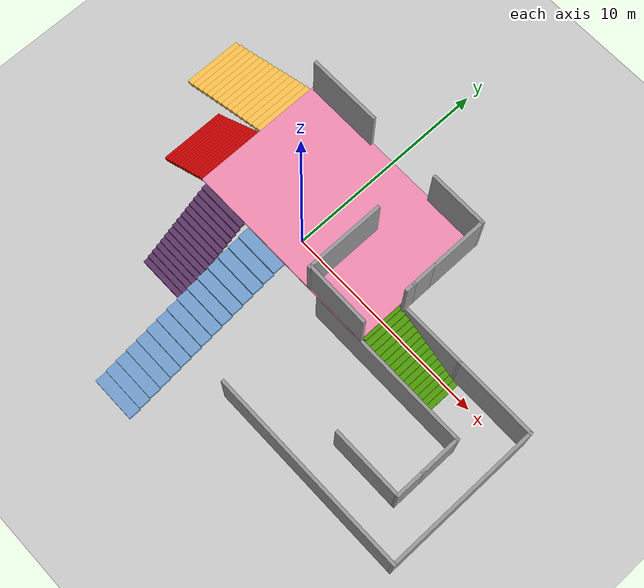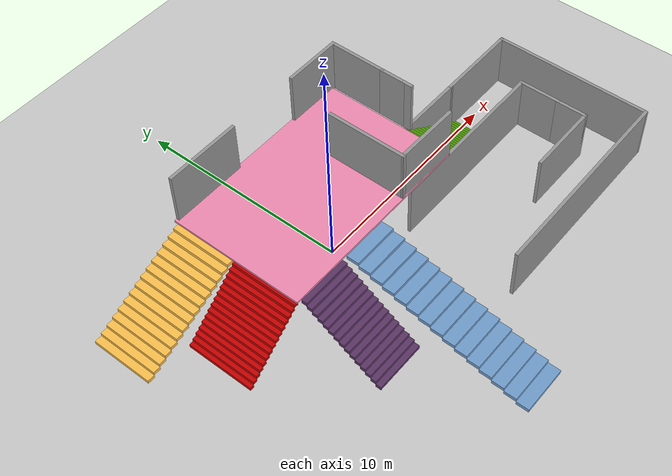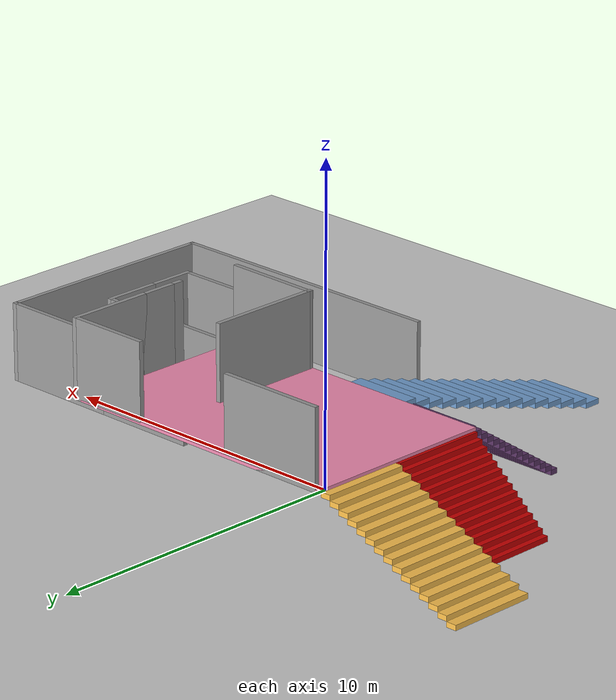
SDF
<sdf version='1.6'>
  <world name='default'>
    <physics name='default_physics' default='0' type='ode'>
      <max_step_size>0.0003</max_step_size>
      <real_time_update_rate>-1</real_time_update_rate>
      <ode>
        <solver>
          <iters>300</iters>
          <type>quick</type>
          <sor>1.3</sor>
          <use_dynamic_moi_rescaling>0</use_dynamic_moi_rescaling>
        </solver>
        <constraints>
          <cfm>0</cfm>
          <erp>0.2</erp>
          <contact_max_correcting_vel>100</contact_max_correcting_vel>
          <contact_surface_layer>0.001</contact_surface_layer>
        </constraints>
      </ode>
      <real_time_factor>1</real_time_factor>
    </physics>
    <model name='ground_plane'>
      <static>1</static>
      <link name='link'>
        <collision name='collision'>
          <geometry>
            <plane>
              <normal>0 0 1</normal>
              <size>100 100</size>
            </plane>
          </geometry>
          <surface>
            <contact>
              <collide_bitmask>65535</collide_bitmask>
              <ode/>
            </contact>
            <friction>
              <ode>
                <mu>100</mu>
                <mu2>50</mu2>
              </ode>
              <torsional>
                <ode/>
              </torsional>
            </friction>
            <bounce/>
          </surface>
          <max_contacts>10</max_contacts>
        </collision>
        <visual name='visual'>
          <cast_shadows>0</cast_shadows>
          <geometry>
            <plane>
              <normal>0 0 1</normal>
              <size>100 100</size>
            </plane>
          </geometry>
          <material>
            <script>
              <uri>file://media/materials/scripts/gazebo.material</uri>
              <name>Gazebo/Grey</name>
            </script>
          </material>
        </visual>
        <self_collide>0</self_collide>
        <enable_wind>0</enable_wind>
        <kinematic>0</kinematic>
      </link>
    </model>
    <light name='sun' type='directional'>
      <cast_shadows>1</cast_shadows>
      <pose frame=''>0 0 10 0 -0 0</pose>
      <diffuse>0.8 0.8 0.8 1</diffuse>
      <specular>0.2 0.2 0.2 1</specular>
      <attenuation>
        <range>1000</range>
        <constant>0.9</constant>
        <linear>0.01</linear>
        <quadratic>0.001</quadratic>
      </attenuation>
      <direction>-0.5 0.1 -0.9</direction>
    </light>
    <gravity>0 0 -9.8</gravity>
    <model name='stair_test_arena'>
      <static>true</static>
      <pose frame=''>1.77029 -2.96555 0 0 -0 0</pose>
      <link name='Floor_0'>
        <pose frame=''>-0.944783 4.29451 2.5 0 -0 0</pose>
        <visual name='Floor_0_Visual_0'>
          <pose frame=''>-0.2 0 0.05 0 -0 0</pose>
          <geometry>
            <box>
              <size>9.4393 6.29101 0.1</size>
            </box>
          </geometry>
          <material>
            <script>
              <uri>file://media/materials/scripts/gazebo.material</uri>
              <name>Gazebo/Pink</name>
            </script>
            <ambient>0.305882 0.603922 0.0235294 1</ambient>
          </material>
          <meta>
            <layer>1</layer>
          </meta>
        </visual>
        <collision name='Floor_0_Collision_0'>
          <geometry>
            <box>
              <size>9.4393 6.29101 0.1</size>
            </box>
          </geometry>
          <max_contacts>10</max_contacts>
          <surface>
            <contact>
              <ode/>
            </contact>
            <bounce/>
            <friction>
              <torsional>
                <ode/>
              </torsional>
              <ode/>
            </friction>
          </surface>
        </collision>
        <self_collide>0</self_collide>
        <enable_wind>0</enable_wind>
        <kinematic>0</kinematic>
      </link>
      <link name='Stairs_0'>
        <visual name='Stairs_0_Visual_0'>
          <pose frame=''>7.09392 2.32468 0.083333 0 -0 -1.5708</pose>
          <geometry>
            <box>
              <size>2 0.25 0.166667</size>
            </box>
          </geometry>
          <material>
            <script>
              <uri>file://media/materials/scripts/gazebo.material</uri>
              <name>Gazebo/Grey</name>
            </script>
            <ambient>0.305882 0.603922 0.0235294 1</ambient>
          </material>
          <meta>
            <layer>0</layer>
          </meta>
        </visual>
        <collision name='Stairs_0_Collision_0'>
          <geometry>
            <box>
              <size>2 0.25 0.166667</size>
            </box>
          </geometry>
          <pose frame=''>7.09392 2.32468 0.083333 0 -0 -1.5708</pose>
          <max_contacts>10</max_contacts>
          <surface>
            <contact>
              <ode/>
            </contact>
            <bounce/>
            <friction>
              <torsional>
                <ode/>
              </torsional>
              <ode/>
            </friction>
          </surface>
        </collision>
        <visual name='Stairs_0_Visual_1'>
          <pose frame=''>6.84392 2.32468 0.25 0 -0 -1.5708</pose>
          <geometry>
            <box>
              <size>2 0.25 0.166667</size>
            </box>
          </geometry>
          <material>
            <script>
              <uri>file://media/materials/scripts/gazebo.material</uri>
              <name>Gazebo/Grey</name>
            </script>
            <ambient>0.305882 0.603922 0.0235294 1</ambient>
          </material>
          <meta>
            <layer>0</layer>
          </meta>
        </visual>
        <collision name='Stairs_0_Collision_1'>
          <geometry>
            <box>
              <size>2 0.25 0.166667</size>
            </box>
          </geometry>
          <pose frame=''>6.84392 2.32468 0.25 0 -0 -1.5708</pose>
          <max_contacts>10</max_contacts>
          <surface>
            <contact>
              <ode/>
            </contact>
            <bounce/>
            <friction>
              <torsional>
                <ode/>
              </torsional>
              <ode/>
            </friction>
          </surface>
        </collision>
        <visual name='Stairs_0_Visual_2'>
          <pose frame=''>6.59392 2.32468 0.416667 0 -0 -1.5708</pose>
          <geometry>
            <box>
              <size>2 0.25 0.166667</size>
            </box>
          </geometry>
          <material>
            <script>
              <uri>file://media/materials/scripts/gazebo.material</uri>
              <name>Gazebo/Grey</name>
            </script>
            <ambient>0.305882 0.603922 0.0235294 1</ambient>
          </material>
          <meta>
            <layer>0</layer>
          </meta>
        </visual>
        <collision name='Stairs_0_Collision_2'>
          <geometry>
            <box>
              <size>2 0.25 0.166667</size>
            </box>
          </geometry>
          <pose frame=''>6.59392 2.32468 0.416667 0 -0 -1.5708</pose>
          <max_contacts>10</max_contacts>
          <surface>
            <contact>
              <ode/>
            </contact>
            <bounce/>
            <friction>
              <torsional>
                <ode/>
              </torsional>
              <ode/>
            </friction>
          </surface>
        </collision>
        <visual name='Stairs_0_Visual_3'>
          <pose frame=''>6.34392 2.32468 0.583333 0 -0 -1.5708</pose>
          <geometry>
            <box>
              <size>2 0.25 0.166667</size>
            </box>
          </geometry>
          <material>
            <script>
              <uri>file://media/materials/scripts/gazebo.material</uri>
              <name>Gazebo/Grey</name>
            </script>
            <ambient>0.305882 0.603922 0.0235294 1</ambient>
          </material>
          <meta>
            <layer>0</layer>
          </meta>
        </visual>
        <collision name='Stairs_0_Collision_3'>
          <geometry>
            <box>
              <size>2 0.25 0.166667</size>
            </box>
          </geometry>
          <pose frame=''>6.34392 2.32468 0.583333 0 -0 -1.5708</pose>
          <max_contacts>10</max_contacts>
          <surface>
            <contact>
              <ode/>
            </contact>
            <bounce/>
            <friction>
              <torsional>
                <ode/>
              </torsional>
              <ode/>
            </friction>
          </surface>
        </collision>
        <visual name='Stairs_0_Visual_4'>
          <pose frame=''>6.09392 2.32468 0.75 0 -0 -1.5708</pose>
          <geometry>
            <box>
              <size>2 0.25 0.166667</size>
            </box>
          </geometry>
          <material>
            <script>
              <uri>file://media/materials/scripts/gazebo.material</uri>
              <name>Gazebo/Grey</name>
            </script>
            <ambient>0.305882 0.603922 0.0235294 1</ambient>
          </material>
          <meta>
            <layer>0</layer>
          </meta>
        </visual>
        <collision name='Stairs_0_Collision_4'>
          <geometry>
            <box>
              <size>2 0.25 0.166667</size>
            </box>
          </geometry>
          <pose frame=''>6.09392 2.32468 0.75 0 -0 -1.5708</pose>
          <max_contacts>10</max_contacts>
          <surface>
            <contact>
              <ode/>
            </contact>
            <bounce/>
            <friction>
              <torsional>
                <ode/>
              </torsional>
              <ode/>
            </friction>
          </surface>
        </collision>
        <visual name='Stairs_0_Visual_5'>
          <pose frame=''>5.84392 2.32468 0.916667 0 -0 -1.5708</pose>
          <geometry>
            <box>
              <size>2 0.25 0.166667</size>
            </box>
          </geometry>
          <material>
            <script>
              <uri>file://media/materials/scripts/gazebo.material</uri>
              <name>Gazebo/Grey</name>
            </script>
            <ambient>0.305882 0.603922 0.0235294 1</ambient>
          </material>
          <meta>
            <layer>0</layer>
          </meta>
        </visual>
        <collision name='Stairs_0_Collision_5'>
          <geometry>
            <box>
              <size>2 0.25 0.166667</size>
            </box>
          </geometry>
          <pose frame=''>5.84392 2.32468 0.916667 0 -0 -1.5708</pose>
          <max_contacts>10</max_contacts>
          <surface>
            <contact>
              <ode/>
            </contact>
            <bounce/>
            <friction>
              <torsional>
                <ode/>
              </torsional>
              <ode/>
            </friction>
          </surface>
        </collision>
        <visual name='Stairs_0_Visual_6'>
          <pose frame=''>5.59392 2.32468 1.08333 0 -0 -1.5708</pose>
          <geometry>
            <box>
              <size>2 0.25 0.166667</size>
            </box>
          </geometry>
          <material>
            <script>
              <uri>file://media/materials/scripts/gazebo.material</uri>
              <name>Gazebo/Grey</name>
            </script>
            <ambient>0.305882 0.603922 0.0235294 1</ambient>
          </material>
          <meta>
            <layer>0</layer>
          </meta>
        </visual>
        <collision name='Stairs_0_Collision_6'>
          <geometry>
            <box>
              <size>2 0.25 0.166667</size>
            </box>
          </geometry>
          <pose frame=''>5.59392 2.32468 1.08333 0 -0 -1.5708</pose>
          <max_contacts>10</max_contacts>
          <surface>
            <contact>
              <ode/>
            </contact>
            <bounce/>
            <friction>
              <torsional>
                <ode/>
              </torsional>
              <ode/>
            </friction>
          </surface>
        </collision>
        <visual name='Stairs_0_Visual_7'>
          <pose frame=''>5.34392 2.32468 1.25 0 -0 -1.5708</pose>
          <geometry>
            <box>
              <size>2 0.25 0.166667</size>
            </box>
          </geometry>
          <material>
            <script>
              <uri>file://media/materials/scripts/gazebo.material</uri>
              <name>Gazebo/Grey</name>
            </script>
            <ambient>0.305882 0.603922 0.0235294 1</ambient>
          </material>
          <meta>
            <layer>0</layer>
          </meta>
        </visual>
        <collision name='Stairs_0_Collision_7'>
          <geometry>
            <box>
              <size>2 0.25 0.166667</size>
            </box>
          </geometry>
          <pose frame=''>5.34392 2.32468 1.25 0 -0 -1.5708</pose>
          <max_contacts>10</max_contacts>
          <surface>
            <contact>
              <ode/>
            </contact>
            <bounce/>
            <friction>
              <torsional>
                <ode/>
              </torsional>
              <ode/>
            </friction>
          </surface>
        </collision>
        <visual name='Stairs_0_Visual_8'>
          <pose frame=''>5.09392 2.32468 1.41667 0 -0 -1.5708</pose>
          <geometry>
            <box>
              <size>2 0.25 0.166667</size>
            </box>
          </geometry>
          <material>
            <script>
              <uri>file://media/materials/scripts/gazebo.material</uri>
              <name>Gazebo/Grey</name>
            </script>
            <ambient>0.305882 0.603922 0.0235294 1</ambient>
          </material>
          <meta>
            <layer>0</layer>
          </meta>
        </visual>
        <collision name='Stairs_0_Collision_8'>
          <geometry>
            <box>
              <size>2 0.25 0.166667</size>
            </box>
          </geometry>
          <pose frame=''>5.09392 2.32468 1.41667 0 -0 -1.5708</pose>
          <max_contacts>10</max_contacts>
          <surface>
            <contact>
              <ode/>
            </contact>
            <bounce/>
            <friction>
              <torsional>
                <ode/>
              </torsional>
              <ode/>
            </friction>
          </surface>
        </collision>
        <visual name='Stairs_0_Visual_9'>
          <pose frame=''>4.84392 2.32468 1.58333 0 -0 -1.5708</pose>
          <geometry>
            <box>
              <size>2 0.25 0.166667</size>
            </box>
          </geometry>
          <material>
            <script>
              <uri>file://media/materials/scripts/gazebo.material</uri>
              <name>Gazebo/Grey</name>
            </script>
            <ambient>0.305882 0.603922 0.0235294 1</ambient>
          </material>
          <meta>
            <layer>0</layer>
          </meta>
        </visual>
        <collision name='Stairs_0_Collision_9'>
          <geometry>
            <box>
              <size>2 0.25 0.166667</size>
            </box>
          </geometry>
          <pose frame=''>4.84392 2.32468 1.58333 0 -0 -1.5708</pose>
          <max_contacts>10</max_contacts>
          <surface>
            <contact>
              <ode/>
            </contact>
            <bounce/>
            <friction>
              <torsional>
                <ode/>
              </torsional>
              <ode/>
            </friction>
          </surface>
        </collision>
        <visual name='Stairs_0_Visual_10'>
          <pose frame=''>4.59392 2.32468 1.75 0 -0 -1.5708</pose>
          <geometry>
            <box>
              <size>2 0.25 0.166667</size>
            </box>
          </geometry>
          <material>
            <script>
              <uri>file://media/materials/scripts/gazebo.material</uri>
              <name>Gazebo/Grey</name>
            </script>
            <ambient>0.305882 0.603922 0.0235294 1</ambient>
          </material>
          <meta>
            <layer>0</layer>
          </meta>
        </visual>
        <collision name='Stairs_0_Collision_10'>
          <geometry>
            <box>
              <size>2 0.25 0.166667</size>
            </box>
          </geometry>
          <pose frame=''>4.59392 2.32468 1.75 0 -0 -1.5708</pose>
          <max_contacts>10</max_contacts>
          <surface>
            <contact>
              <ode/>
            </contact>
            <bounce/>
            <friction>
              <torsional>
                <ode/>
              </torsional>
              <ode/>
            </friction>
          </surface>
        </collision>
        <visual name='Stairs_0_Visual_11'>
          <pose frame=''>4.34392 2.32468 1.91667 0 -0 -1.5708</pose>
          <geometry>
            <box>
              <size>2 0.25 0.166667</size>
            </box>
          </geometry>
          <material>
            <script>
              <uri>file://media/materials/scripts/gazebo.material</uri>
              <name>Gazebo/Grey</name>
            </script>
            <ambient>0.305882 0.603922 0.0235294 1</ambient>
          </material>
          <meta>
            <layer>0</layer>
          </meta>
        </visual>
        <collision name='Stairs_0_Collision_11'>
          <geometry>
            <box>
              <size>2 0.25 0.166667</size>
            </box>
          </geometry>
          <pose frame=''>4.34392 2.32468 1.91667 0 -0 -1.5708</pose>
          <max_contacts>10</max_contacts>
          <surface>
            <contact>
              <ode/>
            </contact>
            <bounce/>
            <friction>
              <torsional>
                <ode/>
              </torsional>
              <ode/>
            </friction>
          </surface>
        </collision>
        <visual name='Stairs_0_Visual_12'>
          <pose frame=''>4.09392 2.32468 2.08333 0 -0 -1.5708</pose>
          <geometry>
            <box>
              <size>2 0.25 0.166667</size>
            </box>
          </geometry>
          <material>
            <script>
              <uri>file://media/materials/scripts/gazebo.material</uri>
              <name>Gazebo/Grey</name>
            </script>
            <ambient>0.305882 0.603922 0.0235294 1</ambient>
          </material>
          <meta>
            <layer>0</layer>
          </meta>
        </visual>
        <collision name='Stairs_0_Collision_12'>
          <geometry>
            <box>
              <size>2 0.25 0.166667</size>
            </box>
          </geometry>
          <pose frame=''>4.09392 2.32468 2.08333 0 -0 -1.5708</pose>
          <max_contacts>10</max_contacts>
          <surface>
            <contact>
              <ode/>
            </contact>
            <bounce/>
            <friction>
              <torsional>
                <ode/>
              </torsional>
              <ode/>
            </friction>
          </surface>
        </collision>
        <visual name='Stairs_0_Visual_13'>
          <pose frame=''>3.84392 2.32468 2.25 0 -0 -1.5708</pose>
          <geometry>
            <box>
              <size>2 0.25 0.166667</size>
            </box>
          </geometry>
          <material>
            <script>
              <uri>file://media/materials/scripts/gazebo.material</uri>
              <name>Gazebo/Grey</name>
            </script>
            <ambient>0.305882 0.603922 0.0235294 1</ambient>
          </material>
          <meta>
            <layer>0</layer>
          </meta>
        </visual>
        <collision name='Stairs_0_Collision_13'>
          <geometry>
            <box>
              <size>2 0.25 0.166667</size>
            </box>
          </geometry>
          <pose frame=''>3.84392 2.32468 2.25 0 -0 -1.5708</pose>
          <max_contacts>10</max_contacts>
          <surface>
            <contact>
              <ode/>
            </contact>
            <bounce/>
            <friction>
              <torsional>
                <ode/>
              </torsional>
              <ode/>
            </friction>
          </surface>
        </collision>
        <visual name='Stairs_0_Visual_14'>
          <pose frame=''>3.59392 2.32468 2.41667 0 -0 -1.5708</pose>
          <geometry>
            <box>
              <size>2 0.25 0.166667</size>
            </box>
          </geometry>
          <material>
            <script>
              <uri>file://media/materials/scripts/gazebo.material</uri>
              <name>Gazebo/Grey</name>
            </script>
            <ambient>0.305882 0.603922 0.0235294 1</ambient>
          </material>
          <meta>
            <layer>0</layer>
          </meta>
        </visual>
        <collision name='Stairs_0_Collision_14'>
          <geometry>
            <box>
              <size>2 0.25 0.166667</size>
            </box>
          </geometry>
          <pose frame=''>3.59392 2.32468 2.41667 0 -0 -1.5708</pose>
          <max_contacts>10</max_contacts>
          <surface>
            <contact>
              <ode/>
            </contact>
            <bounce/>
            <friction>
              <torsional>
                <ode/>
              </torsional>
              <ode/>
            </friction>
          </surface>
        </collision>
        <self_collide>0</self_collide>
        <enable_wind>0</enable_wind>
        <kinematic>0</kinematic>
      </link>
      <link name='Stairs_10'>
        <visual name='Stairs_10_Visual_0'>
          <pose frame=''>-4.44039 -2.47936 0.083333 0 -0 -3.14159</pose>
          <geometry>
            <box>
              <size>2.38 0.25 0.166667</size>
            </box>
          </geometry>
          <material>
            <script>
              <uri>file://media/materials/scripts/gazebo.material</uri>
              <name>Gazebo/Grey</name>
            </script>
            <ambient>0.360784 0.207843 0.4 1</ambient>
          </material>
          <meta>
            <layer>0</layer>
          </meta>
        </visual>
        <collision name='Stairs_10_Collision_0'>
          <geometry>
            <box>
              <size>2.38 0.25 0.166667</size>
            </box>
          </geometry>
          <pose frame=''>-4.44039 -2.47936 0.083333 0 -0 -3.14159</pose>
          <max_contacts>10</max_contacts>
          <surface>
            <contact>
              <ode/>
            </contact>
            <bounce/>
            <friction>
              <torsional>
                <ode/>
              </torsional>
              <ode/>
            </friction>
          </surface>
        </collision>
        <visual name='Stairs_10_Visual_1'>
          <pose frame=''>-4.44039 -2.22936 0.25 0 -0 -3.14159</pose>
          <geometry>
            <box>
              <size>2.38 0.25 0.166667</size>
            </box>
          </geometry>
          <material>
            <script>
              <uri>file://media/materials/scripts/gazebo.material</uri>
              <name>Gazebo/Grey</name>
            </script>
            <ambient>0.360784 0.207843 0.4 1</ambient>
          </material>
          <meta>
            <layer>0</layer>
          </meta>
        </visual>
        <collision name='Stairs_10_Collision_1'>
          <geometry>
            <box>
              <size>2.38 0.25 0.166667</size>
            </box>
          </geometry>
          <pose frame=''>-4.44039 -2.22936 0.25 0 -0 -3.14159</pose>
          <max_contacts>10</max_contacts>
          <surface>
            <contact>
              <ode/>
            </contact>
            <bounce/>
            <friction>
              <torsional>
                <ode/>
              </torsional>
              <ode/>
            </friction>
          </surface>
        </collision>
        <visual name='Stairs_10_Visual_2'>
          <pose frame=''>-4.44039 -1.97936 0.416667 0 -0 -3.14159</pose>
          <geometry>
            <box>
              <size>2.38 0.25 0.166667</size>
            </box>
          </geometry>
          <material>
            <script>
              <uri>file://media/materials/scripts/gazebo.material</uri>
              <name>Gazebo/Grey</name>
            </script>
            <ambient>0.360784 0.207843 0.4 1</ambient>
          </material>
          <meta>
            <layer>0</layer>
          </meta>
        </visual>
        <collision name='Stairs_10_Collision_2'>
          <geometry>
            <box>
              <size>2.38 0.25 0.166667</size>
            </box>
          </geometry>
          <pose frame=''>-4.44039 -1.97936 0.416667 0 -0 -3.14159</pose>
          <max_contacts>10</max_contacts>
          <surface>
            <contact>
              <ode/>
            </contact>
            <bounce/>
            <friction>
              <torsional>
                <ode/>
              </torsional>
              <ode/>
            </friction>
          </surface>
        </collision>
        <visual name='Stairs_10_Visual_3'>
          <pose frame=''>-4.44039 -1.72936 0.583333 0 -0 -3.14159</pose>
          <geometry>
            <box>
              <size>2.38 0.25 0.166667</size>
            </box>
          </geometry>
          <material>
            <script>
              <uri>file://media/materials/scripts/gazebo.material</uri>
              <name>Gazebo/Grey</name>
            </script>
            <ambient>0.360784 0.207843 0.4 1</ambient>
          </material>
          <meta>
            <layer>0</layer>
          </meta>
        </visual>
        <collision name='Stairs_10_Collision_3'>
          <geometry>
            <box>
              <size>2.38 0.25 0.166667</size>
            </box>
          </geometry>
          <pose frame=''>-4.44039 -1.72936 0.583333 0 -0 -3.14159</pose>
          <max_contacts>10</max_contacts>
          <surface>
            <contact>
              <ode/>
            </contact>
            <bounce/>
            <friction>
              <torsional>
                <ode/>
              </torsional>
              <ode/>
            </friction>
          </surface>
        </collision>
        <visual name='Stairs_10_Visual_4'>
          <pose frame=''>-4.44039 -1.47936 0.75 0 -0 -3.14159</pose>
          <geometry>
            <box>
              <size>2.38 0.25 0.166667</size>
            </box>
          </geometry>
          <material>
            <script>
              <uri>file://media/materials/scripts/gazebo.material</uri>
              <name>Gazebo/Grey</name>
            </script>
            <ambient>0.360784 0.207843 0.4 1</ambient>
          </material>
          <meta>
            <layer>0</layer>
          </meta>
        </visual>
        <collision name='Stairs_10_Collision_4'>
          <geometry>
            <box>
              <size>2.38 0.25 0.166667</size>
            </box>
          </geometry>
          <pose frame=''>-4.44039 -1.47936 0.75 0 -0 -3.14159</pose>
          <max_contacts>10</max_contacts>
          <surface>
            <contact>
              <ode/>
            </contact>
            <bounce/>
            <friction>
              <torsional>
                <ode/>
              </torsional>
              <ode/>
            </friction>
          </surface>
        </collision>
        <visual name='Stairs_10_Visual_5'>
          <pose frame=''>-4.44039 -1.22936 0.916667 0 -0 -3.14159</pose>
          <geometry>
            <box>
              <size>2.38 0.25 0.166667</size>
            </box>
          </geometry>
          <material>
            <script>
              <uri>file://media/materials/scripts/gazebo.material</uri>
              <name>Gazebo/Grey</name>
            </script>
            <ambient>0.360784 0.207843 0.4 1</ambient>
          </material>
          <meta>
            <layer>0</layer>
          </meta>
        </visual>
        <collision name='Stairs_10_Collision_5'>
          <geometry>
            <box>
              <size>2.38 0.25 0.166667</size>
            </box>
          </geometry>
          <pose frame=''>-4.44039 -1.22936 0.916667 0 -0 -3.14159</pose>
          <max_contacts>10</max_contacts>
          <surface>
            <contact>
              <ode/>
            </contact>
            <bounce/>
            <friction>
              <torsional>
                <ode/>
              </torsional>
              <ode/>
            </friction>
          </surface>
        </collision>
        <visual name='Stairs_10_Visual_6'>
          <pose frame=''>-4.44039 -0.979357 1.08333 0 -0 -3.14159</pose>
          <geometry>
            <box>
              <size>2.38 0.25 0.166667</size>
            </box>
          </geometry>
          <material>
            <script>
              <uri>file://media/materials/scripts/gazebo.material</uri>
              <name>Gazebo/Grey</name>
            </script>
            <ambient>0.360784 0.207843 0.4 1</ambient>
          </material>
          <meta>
            <layer>0</layer>
          </meta>
        </visual>
        <collision name='Stairs_10_Collision_6'>
          <geometry>
            <box>
              <size>2.38 0.25 0.166667</size>
            </box>
          </geometry>
          <pose frame=''>-4.44039 -0.979357 1.08333 0 -0 -3.14159</pose>
          <max_contacts>10</max_contacts>
          <surface>
            <contact>
              <ode/>
            </contact>
            <bounce/>
            <friction>
              <torsional>
                <ode/>
              </torsional>
              <ode/>
            </friction>
          </surface>
        </collision>
        <visual name='Stairs_10_Visual_7'>
          <pose frame=''>-4.44039 -0.729357 1.25 0 -0 -3.14159</pose>
          <geometry>
            <box>
              <size>2.38 0.25 0.166667</size>
            </box>
          </geometry>
          <material>
            <script>
              <uri>file://media/materials/scripts/gazebo.material</uri>
              <name>Gazebo/Grey</name>
            </script>
            <ambient>0.360784 0.207843 0.4 1</ambient>
          </material>
          <meta>
            <layer>0</layer>
          </meta>
        </visual>
        <collision name='Stairs_10_Collision_7'>
          <geometry>
            <box>
              <size>2.38 0.25 0.166667</size>
            </box>
          </geometry>
          <pose frame=''>-4.44039 -0.729357 1.25 0 -0 -3.14159</pose>
          <max_contacts>10</max_contacts>
          <surface>
            <contact>
              <ode/>
            </contact>
            <bounce/>
            <friction>
              <torsional>
                <ode/>
              </torsional>
              <ode/>
            </friction>
          </surface>
        </collision>
        <visual name='Stairs_10_Visual_8'>
          <pose frame=''>-4.44039 -0.479357 1.41667 0 -0 -3.14159</pose>
          <geometry>
            <box>
              <size>2.38 0.25 0.166667</size>
            </box>
          </geometry>
          <material>
            <script>
              <uri>file://media/materials/scripts/gazebo.material</uri>
              <name>Gazebo/Grey</name>
            </script>
            <ambient>0.360784 0.207843 0.4 1</ambient>
          </material>
          <meta>
            <layer>0</layer>
          </meta>
        </visual>
        <collision name='Stairs_10_Collision_8'>
          <geometry>
            <box>
              <size>2.38 0.25 0.166667</size>
            </box>
          </geometry>
          <pose frame=''>-4.44039 -0.479357 1.41667 0 -0 -3.14159</pose>
          <max_contacts>10</max_contacts>
          <surface>
            <contact>
              <ode/>
            </contact>
            <bounce/>
            <friction>
              <torsional>
                <ode/>
              </torsional>
              <ode/>
            </friction>
          </surface>
        </collision>
        <visual name='Stairs_10_Visual_9'>
          <pose frame=''>-4.44039 -0.229357 1.58333 0 -0 -3.14159</pose>
          <geometry>
            <box>
              <size>2.38 0.25 0.166667</size>
            </box>
          </geometry>
          <material>
            <script>
              <uri>file://media/materials/scripts/gazebo.material</uri>
              <name>Gazebo/Grey</name>
            </script>
            <ambient>0.360784 0.207843 0.4 1</ambient>
          </material>
          <meta>
            <layer>0</layer>
          </meta>
        </visual>
        <collision name='Stairs_10_Collision_9'>
          <geometry>
            <box>
              <size>2.38 0.25 0.166667</size>
            </box>
          </geometry>
          <pose frame=''>-4.44039 -0.229357 1.58333 0 -0 -3.14159</pose>
          <max_contacts>10</max_contacts>
          <surface>
            <contact>
              <ode/>
            </contact>
            <bounce/>
            <friction>
              <torsional>
                <ode/>
              </torsional>
              <ode/>
            </friction>
          </surface>
        </collision>
        <visual name='Stairs_10_Visual_10'>
          <pose frame=''>-4.44039 0.020643 1.75 0 -0 -3.14159</pose>
          <geometry>
            <box>
              <size>2.38 0.25 0.166667</size>
            </box>
          </geometry>
          <material>
            <script>
              <uri>file://media/materials/scripts/gazebo.material</uri>
              <name>Gazebo/Grey</name>
            </script>
            <ambient>0.360784 0.207843 0.4 1</ambient>
          </material>
          <meta>
            <layer>0</layer>
          </meta>
        </visual>
        <collision name='Stairs_10_Collision_10'>
          <geometry>
            <box>
              <size>2.38 0.25 0.166667</size>
            </box>
          </geometry>
          <pose frame=''>-4.44039 0.020643 1.75 0 -0 -3.14159</pose>
          <max_contacts>10</max_contacts>
          <surface>
            <contact>
              <ode/>
            </contact>
            <bounce/>
            <friction>
              <torsional>
                <ode/>
              </torsional>
              <ode/>
            </friction>
          </surface>
        </collision>
        <visual name='Stairs_10_Visual_11'>
          <pose frame=''>-4.44039 0.270643 1.91667 0 -0 -3.14159</pose>
          <geometry>
            <box>
              <size>2.38 0.25 0.166667</size>
            </box>
          </geometry>
          <material>
            <script>
              <uri>file://media/materials/scripts/gazebo.material</uri>
              <name>Gazebo/Grey</name>
            </script>
            <ambient>0.360784 0.207843 0.4 1</ambient>
          </material>
          <meta>
            <layer>0</layer>
          </meta>
        </visual>
        <collision name='Stairs_10_Collision_11'>
          <geometry>
            <box>
              <size>2.38 0.25 0.166667</size>
            </box>
          </geometry>
          <pose frame=''>-4.44039 0.270643 1.91667 0 -0 -3.14159</pose>
          <max_contacts>10</max_contacts>
          <surface>
            <contact>
              <ode/>
            </contact>
            <bounce/>
            <friction>
              <torsional>
                <ode/>
              </torsional>
              <ode/>
            </friction>
          </surface>
        </collision>
        <visual name='Stairs_10_Visual_12'>
          <pose frame=''>-4.44039 0.520643 2.08333 0 -0 -3.14159</pose>
          <geometry>
            <box>
              <size>2.38 0.25 0.166667</size>
            </box>
          </geometry>
          <material>
            <script>
              <uri>file://media/materials/scripts/gazebo.material</uri>
              <name>Gazebo/Grey</name>
            </script>
            <ambient>0.360784 0.207843 0.4 1</ambient>
          </material>
          <meta>
            <layer>0</layer>
          </meta>
        </visual>
        <collision name='Stairs_10_Collision_12'>
          <geometry>
            <box>
              <size>2.38 0.25 0.166667</size>
            </box>
          </geometry>
          <pose frame=''>-4.44039 0.520643 2.08333 0 -0 -3.14159</pose>
          <max_contacts>10</max_contacts>
          <surface>
            <contact>
              <ode/>
            </contact>
            <bounce/>
            <friction>
              <torsional>
                <ode/>
              </torsional>
              <ode/>
            </friction>
          </surface>
        </collision>
        <visual name='Stairs_10_Visual_13'>
          <pose frame=''>-4.44039 0.770643 2.25 0 -0 -3.14159</pose>
          <geometry>
            <box>
              <size>2.38 0.25 0.166667</size>
            </box>
          </geometry>
          <material>
            <script>
              <uri>file://media/materials/scripts/gazebo.material</uri>
              <name>Gazebo/Grey</name>
            </script>
            <ambient>0.360784 0.207843 0.4 1</ambient>
          </material>
          <meta>
            <layer>0</layer>
          </meta>
        </visual>
        <collision name='Stairs_10_Collision_13'>
          <geometry>
            <box>
              <size>2.38 0.25 0.166667</size>
            </box>
          </geometry>
          <pose frame=''>-4.44039 0.770643 2.25 0 -0 -3.14159</pose>
          <max_contacts>10</max_contacts>
          <surface>
            <contact>
              <ode/>
            </contact>
            <bounce/>
            <friction>
              <torsional>
                <ode/>
              </torsional>
              <ode/>
            </friction>
          </surface>
        </collision>
        <visual name='Stairs_10_Visual_14'>
          <pose frame=''>-4.44039 1.02064 2.41667 0 -0 -3.14159</pose>
          <geometry>
            <box>
              <size>2.38 0.25 0.166667</size>
            </box>
          </geometry>
          <material>
            <script>
              <uri>file://media/materials/scripts/gazebo.material</uri>
              <name>Gazebo/Grey</name>
            </script>
            <ambient>0.360784 0.207843 0.4 1</ambient>
          </material>
          <meta>
            <layer>0</layer>
          </meta>
        </visual>
        <collision name='Stairs_10_Collision_14'>
          <geometry>
            <box>
              <size>2.38 0.25 0.166667</size>
            </box>
          </geometry>
          <pose frame=''>-4.44039 1.02064 2.41667 0 -0 -3.14159</pose>
          <max_contacts>10</max_contacts>
          <surface>
            <contact>
              <ode/>
            </contact>
            <bounce/>
            <friction>
              <torsional>
                <ode/>
              </torsional>
              <ode/>
            </friction>
          </surface>
        </collision>
        <self_collide>0</self_collide>
        <enable_wind>0</enable_wind>
        <kinematic>0</kinematic>
      </link>
      <link name='Stairs_3'>
        <visual name='Stairs_3_Visual_0'>
          <pose frame=''>-10.6336 5.83002 0.083333 0 -0 1.5708</pose>
          <geometry>
            <box>
              <size>2.86201 0.333333 0.166667</size>
            </box>
          </geometry>
          <material>
            <script>
              <uri>file://media/materials/scripts/gazebo.material</uri>
              <name>Gazebo/Grey</name>
            </script>
            <ambient>1 0.764706 0.305882 1</ambient>
          </material>
          <meta>
            <layer>0</layer>
          </meta>
        </visual>
        <collision name='Stairs_3_Collision_0'>
          <geometry>
            <box>
              <size>2.86201 0.333333 0.166667</size>
            </box>
          </geometry>
          <pose frame=''>-10.6336 5.83002 0.083333 0 -0 1.5708</pose>
          <max_contacts>10</max_contacts>
          <surface>
            <contact>
              <ode/>
            </contact>
            <bounce/>
            <friction>
              <torsional>
                <ode/>
              </torsional>
              <ode/>
            </friction>
          </surface>
        </collision>
        <visual name='Stairs_3_Visual_1'>
          <pose frame=''>-10.3003 5.83002 0.25 0 -0 1.5708</pose>
          <geometry>
            <box>
              <size>2.86201 0.333333 0.166667</size>
            </box>
          </geometry>
          <material>
            <script>
              <uri>file://media/materials/scripts/gazebo.material</uri>
              <name>Gazebo/Grey</name>
            </script>
            <ambient>1 0.764706 0.305882 1</ambient>
          </material>
          <meta>
            <layer>0</layer>
          </meta>
        </visual>
        <collision name='Stairs_3_Collision_1'>
          <geometry>
            <box>
              <size>2.86201 0.333333 0.166667</size>
            </box>
          </geometry>
          <pose frame=''>-10.3003 5.83002 0.25 0 -0 1.5708</pose>
          <max_contacts>10</max_contacts>
          <surface>
            <contact>
              <ode/>
            </contact>
            <bounce/>
            <friction>
              <torsional>
                <ode/>
              </torsional>
              <ode/>
            </friction>
          </surface>
        </collision>
        <visual name='Stairs_3_Visual_2'>
          <pose frame=''>-9.96695 5.83002 0.416667 0 -0 1.5708</pose>
          <geometry>
            <box>
              <size>2.86201 0.333333 0.166667</size>
            </box>
          </geometry>
          <material>
            <script>
              <uri>file://media/materials/scripts/gazebo.material</uri>
              <name>Gazebo/Grey</name>
            </script>
            <ambient>1 0.764706 0.305882 1</ambient>
          </material>
          <meta>
            <layer>0</layer>
          </meta>
        </visual>
        <collision name='Stairs_3_Collision_2'>
          <geometry>
            <box>
              <size>2.86201 0.333333 0.166667</size>
            </box>
          </geometry>
          <pose frame=''>-9.96695 5.83002 0.416667 0 -0 1.5708</pose>
          <max_contacts>10</max_contacts>
          <surface>
            <contact>
              <ode/>
            </contact>
            <bounce/>
            <friction>
              <torsional>
                <ode/>
              </torsional>
              <ode/>
            </friction>
          </surface>
        </collision>
        <visual name='Stairs_3_Visual_3'>
          <pose frame=''>-9.63362 5.83002 0.583333 0 -0 1.5708</pose>
          <geometry>
            <box>
              <size>2.86201 0.333333 0.166667</size>
            </box>
          </geometry>
          <material>
            <script>
              <uri>file://media/materials/scripts/gazebo.material</uri>
              <name>Gazebo/Grey</name>
            </script>
            <ambient>1 0.764706 0.305882 1</ambient>
          </material>
          <meta>
            <layer>0</layer>
          </meta>
        </visual>
        <collision name='Stairs_3_Collision_3'>
          <geometry>
            <box>
              <size>2.86201 0.333333 0.166667</size>
            </box>
          </geometry>
          <pose frame=''>-9.63362 5.83002 0.583333 0 -0 1.5708</pose>
          <max_contacts>10</max_contacts>
          <surface>
            <contact>
              <ode/>
            </contact>
            <bounce/>
            <friction>
              <torsional>
                <ode/>
              </torsional>
              <ode/>
            </friction>
          </surface>
        </collision>
        <visual name='Stairs_3_Visual_4'>
          <pose frame=''>-9.30028 5.83002 0.75 0 -0 1.5708</pose>
          <geometry>
            <box>
              <size>2.86201 0.333333 0.166667</size>
            </box>
          </geometry>
          <material>
            <script>
              <uri>file://media/materials/scripts/gazebo.material</uri>
              <name>Gazebo/Grey</name>
            </script>
            <ambient>1 0.764706 0.305882 1</ambient>
          </material>
          <meta>
            <layer>0</layer>
          </meta>
        </visual>
        <collision name='Stairs_3_Collision_4'>
          <geometry>
            <box>
              <size>2.86201 0.333333 0.166667</size>
            </box>
          </geometry>
          <pose frame=''>-9.30028 5.83002 0.75 0 -0 1.5708</pose>
          <max_contacts>10</max_contacts>
          <surface>
            <contact>
              <ode/>
            </contact>
            <bounce/>
            <friction>
              <torsional>
                <ode/>
              </torsional>
              <ode/>
            </friction>
          </surface>
        </collision>
        <visual name='Stairs_3_Visual_5'>
          <pose frame=''>-8.96695 5.83002 0.916667 0 -0 1.5708</pose>
          <geometry>
            <box>
              <size>2.86201 0.333333 0.166667</size>
            </box>
          </geometry>
          <material>
            <script>
              <uri>file://media/materials/scripts/gazebo.material</uri>
              <name>Gazebo/Grey</name>
            </script>
            <ambient>1 0.764706 0.305882 1</ambient>
          </material>
          <meta>
            <layer>0</layer>
          </meta>
        </visual>
        <collision name='Stairs_3_Collision_5'>
          <geometry>
            <box>
              <size>2.86201 0.333333 0.166667</size>
            </box>
          </geometry>
          <pose frame=''>-8.96695 5.83002 0.916667 0 -0 1.5708</pose>
          <max_contacts>10</max_contacts>
          <surface>
            <contact>
              <ode/>
            </contact>
            <bounce/>
            <friction>
              <torsional>
                <ode/>
              </torsional>
              <ode/>
            </friction>
          </surface>
        </collision>
        <visual name='Stairs_3_Visual_6'>
          <pose frame=''>-8.63362 5.83002 1.08333 0 -0 1.5708</pose>
          <geometry>
            <box>
              <size>2.86201 0.333333 0.166667</size>
            </box>
          </geometry>
          <material>
            <script>
              <uri>file://media/materials/scripts/gazebo.material</uri>
              <name>Gazebo/Grey</name>
            </script>
            <ambient>1 0.764706 0.305882 1</ambient>
          </material>
          <meta>
            <layer>0</layer>
          </meta>
        </visual>
        <collision name='Stairs_3_Collision_6'>
          <geometry>
            <box>
              <size>2.86201 0.333333 0.166667</size>
            </box>
          </geometry>
          <pose frame=''>-8.63362 5.83002 1.08333 0 -0 1.5708</pose>
          <max_contacts>10</max_contacts>
          <surface>
            <contact>
              <ode/>
            </contact>
            <bounce/>
            <friction>
              <torsional>
                <ode/>
              </torsional>
              <ode/>
            </friction>
          </surface>
        </collision>
        <visual name='Stairs_3_Visual_7'>
          <pose frame=''>-8.30028 5.83002 1.25 0 -0 1.5708</pose>
          <geometry>
            <box>
              <size>2.86201 0.333333 0.166667</size>
            </box>
          </geometry>
          <material>
            <script>
              <uri>file://media/materials/scripts/gazebo.material</uri>
              <name>Gazebo/Grey</name>
            </script>
            <ambient>1 0.764706 0.305882 1</ambient>
          </material>
          <meta>
            <layer>0</layer>
          </meta>
        </visual>
        <collision name='Stairs_3_Collision_7'>
          <geometry>
            <box>
              <size>2.86201 0.333333 0.166667</size>
            </box>
          </geometry>
          <pose frame=''>-8.30028 5.83002 1.25 0 -0 1.5708</pose>
          <max_contacts>10</max_contacts>
          <surface>
            <contact>
              <ode/>
            </contact>
            <bounce/>
            <friction>
              <torsional>
                <ode/>
              </torsional>
              <ode/>
            </friction>
          </surface>
        </collision>
        <visual name='Stairs_3_Visual_8'>
          <pose frame=''>-7.96695 5.83002 1.41667 0 -0 1.5708</pose>
          <geometry>
            <box>
              <size>2.86201 0.333333 0.166667</size>
            </box>
          </geometry>
          <material>
            <script>
              <uri>file://media/materials/scripts/gazebo.material</uri>
              <name>Gazebo/Grey</name>
            </script>
            <ambient>1 0.764706 0.305882 1</ambient>
          </material>
          <meta>
            <layer>0</layer>
          </meta>
        </visual>
        <collision name='Stairs_3_Collision_8'>
          <geometry>
            <box>
              <size>2.86201 0.333333 0.166667</size>
            </box>
          </geometry>
          <pose frame=''>-7.96695 5.83002 1.41667 0 -0 1.5708</pose>
          <max_contacts>10</max_contacts>
          <surface>
            <contact>
              <ode/>
            </contact>
            <bounce/>
            <friction>
              <torsional>
                <ode/>
              </torsional>
              <ode/>
            </friction>
          </surface>
        </collision>
        <visual name='Stairs_3_Visual_9'>
          <pose frame=''>-7.63361 5.83002 1.58333 0 -0 1.5708</pose>
          <geometry>
            <box>
              <size>2.86201 0.333333 0.166667</size>
            </box>
          </geometry>
          <material>
            <script>
              <uri>file://media/materials/scripts/gazebo.material</uri>
              <name>Gazebo/Grey</name>
            </script>
            <ambient>1 0.764706 0.305882 1</ambient>
          </material>
          <meta>
            <layer>0</layer>
          </meta>
        </visual>
        <collision name='Stairs_3_Collision_9'>
          <geometry>
            <box>
              <size>2.86201 0.333333 0.166667</size>
            </box>
          </geometry>
          <pose frame=''>-7.63361 5.83002 1.58333 0 -0 1.5708</pose>
          <max_contacts>10</max_contacts>
          <surface>
            <contact>
              <ode/>
            </contact>
            <bounce/>
            <friction>
              <torsional>
                <ode/>
              </torsional>
              <ode/>
            </friction>
          </surface>
        </collision>
        <visual name='Stairs_3_Visual_10'>
          <pose frame=''>-7.30028 5.83002 1.75 0 -0 1.5708</pose>
          <geometry>
            <box>
              <size>2.86201 0.333333 0.166667</size>
            </box>
          </geometry>
          <material>
            <script>
              <uri>file://media/materials/scripts/gazebo.material</uri>
              <name>Gazebo/Grey</name>
            </script>
            <ambient>1 0.764706 0.305882 1</ambient>
          </material>
          <meta>
            <layer>0</layer>
          </meta>
        </visual>
        <collision name='Stairs_3_Collision_10'>
          <geometry>
            <box>
              <size>2.86201 0.333333 0.166667</size>
            </box>
          </geometry>
          <pose frame=''>-7.30028 5.83002 1.75 0 -0 1.5708</pose>
          <max_contacts>10</max_contacts>
          <surface>
            <contact>
              <ode/>
            </contact>
            <bounce/>
            <friction>
              <torsional>
                <ode/>
              </torsional>
              <ode/>
            </friction>
          </surface>
        </collision>
        <visual name='Stairs_3_Visual_11'>
          <pose frame=''>-6.96695 5.83002 1.91667 0 -0 1.5708</pose>
          <geometry>
            <box>
              <size>2.86201 0.333333 0.166667</size>
            </box>
          </geometry>
          <material>
            <script>
              <uri>file://media/materials/scripts/gazebo.material</uri>
              <name>Gazebo/Grey</name>
            </script>
            <ambient>1 0.764706 0.305882 1</ambient>
          </material>
          <meta>
            <layer>0</layer>
          </meta>
        </visual>
        <collision name='Stairs_3_Collision_11'>
          <geometry>
            <box>
              <size>2.86201 0.333333 0.166667</size>
            </box>
          </geometry>
          <pose frame=''>-6.96695 5.83002 1.91667 0 -0 1.5708</pose>
          <max_contacts>10</max_contacts>
          <surface>
            <contact>
              <ode/>
            </contact>
            <bounce/>
            <friction>
              <torsional>
                <ode/>
              </torsional>
              <ode/>
            </friction>
          </surface>
        </collision>
        <visual name='Stairs_3_Visual_12'>
          <pose frame=''>-6.63361 5.83002 2.08333 0 -0 1.5708</pose>
          <geometry>
            <box>
              <size>2.86201 0.333333 0.166667</size>
            </box>
          </geometry>
          <material>
            <script>
              <uri>file://media/materials/scripts/gazebo.material</uri>
              <name>Gazebo/Grey</name>
            </script>
            <ambient>1 0.764706 0.305882 1</ambient>
          </material>
          <meta>
            <layer>0</layer>
          </meta>
        </visual>
        <collision name='Stairs_3_Collision_12'>
          <geometry>
            <box>
              <size>2.86201 0.333333 0.166667</size>
            </box>
          </geometry>
          <pose frame=''>-6.63361 5.83002 2.08333 0 -0 1.5708</pose>
          <max_contacts>10</max_contacts>
          <surface>
            <contact>
              <ode/>
            </contact>
            <bounce/>
            <friction>
              <torsional>
                <ode/>
              </torsional>
              <ode/>
            </friction>
          </surface>
        </collision>
        <visual name='Stairs_3_Visual_13'>
          <pose frame=''>-6.30028 5.83002 2.25 0 -0 1.5708</pose>
          <geometry>
            <box>
              <size>2.86201 0.333333 0.166667</size>
            </box>
          </geometry>
          <material>
            <script>
              <uri>file://media/materials/scripts/gazebo.material</uri>
              <name>Gazebo/Grey</name>
            </script>
            <ambient>1 0.764706 0.305882 1</ambient>
          </material>
          <meta>
            <layer>0</layer>
          </meta>
        </visual>
        <collision name='Stairs_3_Collision_13'>
          <geometry>
            <box>
              <size>2.86201 0.333333 0.166667</size>
            </box>
          </geometry>
          <pose frame=''>-6.30028 5.83002 2.25 0 -0 1.5708</pose>
          <max_contacts>10</max_contacts>
          <surface>
            <contact>
              <ode/>
            </contact>
            <bounce/>
            <friction>
              <torsional>
                <ode/>
              </torsional>
              <ode/>
            </friction>
          </surface>
        </collision>
        <visual name='Stairs_3_Visual_14'>
          <pose frame=''>-5.96695 5.83002 2.41667 0 -0 1.5708</pose>
          <geometry>
            <box>
              <size>2.86201 0.333333 0.166667</size>
            </box>
          </geometry>
          <material>
            <script>
              <uri>file://media/materials/scripts/gazebo.material</uri>
              <name>Gazebo/Grey</name>
            </script>
            <ambient>1 0.764706 0.305882 1</ambient>
          </material>
          <meta>
            <layer>0</layer>
          </meta>
        </visual>
        <collision name='Stairs_3_Collision_14'>
          <geometry>
            <box>
              <size>2.86201 0.333333 0.166667</size>
            </box>
          </geometry>
          <pose frame=''>-5.96695 5.83002 2.41667 0 -0 1.5708</pose>
          <max_contacts>10</max_contacts>
          <surface>
            <contact>
              <ode/>
            </contact>
            <bounce/>
            <friction>
              <torsional>
                <ode/>
              </torsional>
              <ode/>
            </friction>
          </surface>
        </collision>
        <self_collide>0</self_collide>
        <enable_wind>0</enable_wind>
        <kinematic>0</kinematic>
      </link>
      <link name='Stairs_6'>
        <visual name='Stairs_6_Visual_0'>
          <pose frame=''>-8.56681 2.75903 0.083333 0 -0 1.5708</pose>
          <geometry>
            <box>
              <size>3.12802 0.192546 0.166667</size>
            </box>
          </geometry>
          <material>
            <script>
              <uri>file://media/materials/scripts/gazebo.material</uri>
              <name>Gazebo/Grey</name>
            </script>
            <ambient>0.8 0 0 1</ambient>
          </material>
          <meta>
            <layer>0</layer>
          </meta>
        </visual>
        <collision name='Stairs_6_Collision_0'>
          <geometry>
            <box>
              <size>3.12802 0.192546 0.166667</size>
            </box>
          </geometry>
          <pose frame=''>-8.56681 2.75903 0.083333 0 -0 1.5708</pose>
          <max_contacts>10</max_contacts>
          <surface>
            <contact>
              <ode/>
            </contact>
            <bounce/>
            <friction>
              <torsional>
                <ode/>
              </torsional>
              <ode/>
            </friction>
          </surface>
        </collision>
        <visual name='Stairs_6_Visual_1'>
          <pose frame=''>-8.37426 2.75903 0.25 0 -0 1.5708</pose>
          <geometry>
            <box>
              <size>3.12802 0.192546 0.166667</size>
            </box>
          </geometry>
          <material>
            <script>
              <uri>file://media/materials/scripts/gazebo.material</uri>
              <name>Gazebo/Grey</name>
            </script>
            <ambient>0.8 0 0 1</ambient>
          </material>
          <meta>
            <layer>0</layer>
          </meta>
        </visual>
        <collision name='Stairs_6_Collision_1'>
          <geometry>
            <box>
              <size>3.12802 0.192546 0.166667</size>
            </box>
          </geometry>
          <pose frame=''>-8.37426 2.75903 0.25 0 -0 1.5708</pose>
          <max_contacts>10</max_contacts>
          <surface>
            <contact>
              <ode/>
            </contact>
            <bounce/>
            <friction>
              <torsional>
                <ode/>
              </torsional>
              <ode/>
            </friction>
          </surface>
        </collision>
        <visual name='Stairs_6_Visual_2'>
          <pose frame=''>-8.18172 2.75903 0.416667 0 -0 1.5708</pose>
          <geometry>
            <box>
              <size>3.12802 0.192546 0.166667</size>
            </box>
          </geometry>
          <material>
            <script>
              <uri>file://media/materials/scripts/gazebo.material</uri>
              <name>Gazebo/Grey</name>
            </script>
            <ambient>0.8 0 0 1</ambient>
          </material>
          <meta>
            <layer>0</layer>
          </meta>
        </visual>
        <collision name='Stairs_6_Collision_2'>
          <geometry>
            <box>
              <size>3.12802 0.192546 0.166667</size>
            </box>
          </geometry>
          <pose frame=''>-8.18172 2.75903 0.416667 0 -0 1.5708</pose>
          <max_contacts>10</max_contacts>
          <surface>
            <contact>
              <ode/>
            </contact>
            <bounce/>
            <friction>
              <torsional>
                <ode/>
              </torsional>
              <ode/>
            </friction>
          </surface>
        </collision>
        <visual name='Stairs_6_Visual_3'>
          <pose frame=''>-7.98917 2.75903 0.583333 0 -0 1.5708</pose>
          <geometry>
            <box>
              <size>3.12802 0.192546 0.166667</size>
            </box>
          </geometry>
          <material>
            <script>
              <uri>file://media/materials/scripts/gazebo.material</uri>
              <name>Gazebo/Grey</name>
            </script>
            <ambient>0.8 0 0 1</ambient>
          </material>
          <meta>
            <layer>0</layer>
          </meta>
        </visual>
        <collision name='Stairs_6_Collision_3'>
          <geometry>
            <box>
              <size>3.12802 0.192546 0.166667</size>
            </box>
          </geometry>
          <pose frame=''>-7.98917 2.75903 0.583333 0 -0 1.5708</pose>
          <max_contacts>10</max_contacts>
          <surface>
            <contact>
              <ode/>
            </contact>
            <bounce/>
            <friction>
              <torsional>
                <ode/>
              </torsional>
              <ode/>
            </friction>
          </surface>
        </collision>
        <visual name='Stairs_6_Visual_4'>
          <pose frame=''>-7.79662 2.75903 0.75 0 -0 1.5708</pose>
          <geometry>
            <box>
              <size>3.12802 0.192546 0.166667</size>
            </box>
          </geometry>
          <material>
            <script>
              <uri>file://media/materials/scripts/gazebo.material</uri>
              <name>Gazebo/Grey</name>
            </script>
            <ambient>0.8 0 0 1</ambient>
          </material>
          <meta>
            <layer>0</layer>
          </meta>
        </visual>
        <collision name='Stairs_6_Collision_4'>
          <geometry>
            <box>
              <size>3.12802 0.192546 0.166667</size>
            </box>
          </geometry>
          <pose frame=''>-7.79662 2.75903 0.75 0 -0 1.5708</pose>
          <max_contacts>10</max_contacts>
          <surface>
            <contact>
              <ode/>
            </contact>
            <bounce/>
            <friction>
              <torsional>
                <ode/>
              </torsional>
              <ode/>
            </friction>
          </surface>
        </collision>
        <visual name='Stairs_6_Visual_5'>
          <pose frame=''>-7.60407 2.75903 0.916667 0 -0 1.5708</pose>
          <geometry>
            <box>
              <size>3.12802 0.192546 0.166667</size>
            </box>
          </geometry>
          <material>
            <script>
              <uri>file://media/materials/scripts/gazebo.material</uri>
              <name>Gazebo/Grey</name>
            </script>
            <ambient>0.8 0 0 1</ambient>
          </material>
          <meta>
            <layer>0</layer>
          </meta>
        </visual>
        <collision name='Stairs_6_Collision_5'>
          <geometry>
            <box>
              <size>3.12802 0.192546 0.166667</size>
            </box>
          </geometry>
          <pose frame=''>-7.60407 2.75903 0.916667 0 -0 1.5708</pose>
          <max_contacts>10</max_contacts>
          <surface>
            <contact>
              <ode/>
            </contact>
            <bounce/>
            <friction>
              <torsional>
                <ode/>
              </torsional>
              <ode/>
            </friction>
          </surface>
        </collision>
        <visual name='Stairs_6_Visual_6'>
          <pose frame=''>-7.41153 2.75903 1.08333 0 -0 1.5708</pose>
          <geometry>
            <box>
              <size>3.12802 0.192546 0.166667</size>
            </box>
          </geometry>
          <material>
            <script>
              <uri>file://media/materials/scripts/gazebo.material</uri>
              <name>Gazebo/Grey</name>
            </script>
            <ambient>0.8 0 0 1</ambient>
          </material>
          <meta>
            <layer>0</layer>
          </meta>
        </visual>
        <collision name='Stairs_6_Collision_6'>
          <geometry>
            <box>
              <size>3.12802 0.192546 0.166667</size>
            </box>
          </geometry>
          <pose frame=''>-7.41153 2.75903 1.08333 0 -0 1.5708</pose>
          <max_contacts>10</max_contacts>
          <surface>
            <contact>
              <ode/>
            </contact>
            <bounce/>
            <friction>
              <torsional>
                <ode/>
              </torsional>
              <ode/>
            </friction>
          </surface>
        </collision>
        <visual name='Stairs_6_Visual_7'>
          <pose frame=''>-7.21898 2.75903 1.25 0 -0 1.5708</pose>
          <geometry>
            <box>
              <size>3.12802 0.192546 0.166667</size>
            </box>
          </geometry>
          <material>
            <script>
              <uri>file://media/materials/scripts/gazebo.material</uri>
              <name>Gazebo/Grey</name>
            </script>
            <ambient>0.8 0 0 1</ambient>
          </material>
          <meta>
            <layer>0</layer>
          </meta>
        </visual>
        <collision name='Stairs_6_Collision_7'>
          <geometry>
            <box>
              <size>3.12802 0.192546 0.166667</size>
            </box>
          </geometry>
          <pose frame=''>-7.21898 2.75903 1.25 0 -0 1.5708</pose>
          <max_contacts>10</max_contacts>
          <surface>
            <contact>
              <ode/>
            </contact>
            <bounce/>
            <friction>
              <torsional>
                <ode/>
              </torsional>
              <ode/>
            </friction>
          </surface>
        </collision>
        <visual name='Stairs_6_Visual_8'>
          <pose frame=''>-7.02644 2.75903 1.41667 0 -0 1.5708</pose>
          <geometry>
            <box>
              <size>3.12802 0.192546 0.166667</size>
            </box>
          </geometry>
          <material>
            <script>
              <uri>file://media/materials/scripts/gazebo.material</uri>
              <name>Gazebo/Grey</name>
            </script>
            <ambient>0.8 0 0 1</ambient>
          </material>
          <meta>
            <layer>0</layer>
          </meta>
        </visual>
        <collision name='Stairs_6_Collision_8'>
          <geometry>
            <box>
              <size>3.12802 0.192546 0.166667</size>
            </box>
          </geometry>
          <pose frame=''>-7.02644 2.75903 1.41667 0 -0 1.5708</pose>
          <max_contacts>10</max_contacts>
          <surface>
            <contact>
              <ode/>
            </contact>
            <bounce/>
            <friction>
              <torsional>
                <ode/>
              </torsional>
              <ode/>
            </friction>
          </surface>
        </collision>
        <visual name='Stairs_6_Visual_9'>
          <pose frame=''>-6.83389 2.75903 1.58333 0 -0 1.5708</pose>
          <geometry>
            <box>
              <size>3.12802 0.192546 0.166667</size>
            </box>
          </geometry>
          <material>
            <script>
              <uri>file://media/materials/scripts/gazebo.material</uri>
              <name>Gazebo/Grey</name>
            </script>
            <ambient>0.8 0 0 1</ambient>
          </material>
          <meta>
            <layer>0</layer>
          </meta>
        </visual>
        <collision name='Stairs_6_Collision_9'>
          <geometry>
            <box>
              <size>3.12802 0.192546 0.166667</size>
            </box>
          </geometry>
          <pose frame=''>-6.83389 2.75903 1.58333 0 -0 1.5708</pose>
          <max_contacts>10</max_contacts>
          <surface>
            <contact>
              <ode/>
            </contact>
            <bounce/>
            <friction>
              <torsional>
                <ode/>
              </torsional>
              <ode/>
            </friction>
          </surface>
        </collision>
        <visual name='Stairs_6_Visual_10'>
          <pose frame=''>-6.64134 2.75903 1.75 0 -0 1.5708</pose>
          <geometry>
            <box>
              <size>3.12802 0.192546 0.166667</size>
            </box>
          </geometry>
          <material>
            <script>
              <uri>file://media/materials/scripts/gazebo.material</uri>
              <name>Gazebo/Grey</name>
            </script>
            <ambient>0.8 0 0 1</ambient>
          </material>
          <meta>
            <layer>0</layer>
          </meta>
        </visual>
        <collision name='Stairs_6_Collision_10'>
          <geometry>
            <box>
              <size>3.12802 0.192546 0.166667</size>
            </box>
          </geometry>
          <pose frame=''>-6.64134 2.75903 1.75 0 -0 1.5708</pose>
          <max_contacts>10</max_contacts>
          <surface>
            <contact>
              <ode/>
            </contact>
            <bounce/>
            <friction>
              <torsional>
                <ode/>
              </torsional>
              <ode/>
            </friction>
          </surface>
        </collision>
        <visual name='Stairs_6_Visual_11'>
          <pose frame=''>-6.4488 2.75903 1.91667 0 -0 1.5708</pose>
          <geometry>
            <box>
              <size>3.12802 0.192546 0.166667</size>
            </box>
          </geometry>
          <material>
            <script>
              <uri>file://media/materials/scripts/gazebo.material</uri>
              <name>Gazebo/Grey</name>
            </script>
            <ambient>0.8 0 0 1</ambient>
          </material>
          <meta>
            <layer>0</layer>
          </meta>
        </visual>
        <collision name='Stairs_6_Collision_11'>
          <geometry>
            <box>
              <size>3.12802 0.192546 0.166667</size>
            </box>
          </geometry>
          <pose frame=''>-6.4488 2.75903 1.91667 0 -0 1.5708</pose>
          <max_contacts>10</max_contacts>
          <surface>
            <contact>
              <ode/>
            </contact>
            <bounce/>
            <friction>
              <torsional>
                <ode/>
              </torsional>
              <ode/>
            </friction>
          </surface>
        </collision>
        <visual name='Stairs_6_Visual_12'>
          <pose frame=''>-6.25625 2.75903 2.08333 0 -0 1.5708</pose>
          <geometry>
            <box>
              <size>3.12802 0.192546 0.166667</size>
            </box>
          </geometry>
          <material>
            <script>
              <uri>file://media/materials/scripts/gazebo.material</uri>
              <name>Gazebo/Grey</name>
            </script>
            <ambient>0.8 0 0 1</ambient>
          </material>
          <meta>
            <layer>0</layer>
          </meta>
        </visual>
        <collision name='Stairs_6_Collision_12'>
          <geometry>
            <box>
              <size>3.12802 0.192546 0.166667</size>
            </box>
          </geometry>
          <pose frame=''>-6.25625 2.75903 2.08333 0 -0 1.5708</pose>
          <max_contacts>10</max_contacts>
          <surface>
            <contact>
              <ode/>
            </contact>
            <bounce/>
            <friction>
              <torsional>
                <ode/>
              </torsional>
              <ode/>
            </friction>
          </surface>
        </collision>
        <visual name='Stairs_6_Visual_13'>
          <pose frame=''>-6.0637 2.75903 2.25 0 -0 1.5708</pose>
          <geometry>
            <box>
              <size>3.12802 0.192546 0.166667</size>
            </box>
          </geometry>
          <material>
            <script>
              <uri>file://media/materials/scripts/gazebo.material</uri>
              <name>Gazebo/Grey</name>
            </script>
            <ambient>0.8 0 0 1</ambient>
          </material>
          <meta>
            <layer>0</layer>
          </meta>
        </visual>
        <collision name='Stairs_6_Collision_13'>
          <geometry>
            <box>
              <size>3.12802 0.192546 0.166667</size>
            </box>
          </geometry>
          <pose frame=''>-6.0637 2.75903 2.25 0 -0 1.5708</pose>
          <max_contacts>10</max_contacts>
          <surface>
            <contact>
              <ode/>
            </contact>
            <bounce/>
            <friction>
              <torsional>
                <ode/>
              </torsional>
              <ode/>
            </friction>
          </surface>
        </collision>
        <visual name='Stairs_6_Visual_14'>
          <pose frame=''>-5.87116 2.75903 2.41667 0 -0 1.5708</pose>
          <geometry>
            <box>
              <size>3.12802 0.192546 0.166667</size>
            </box>
          </geometry>
          <material>
            <script>
              <uri>file://media/materials/scripts/gazebo.material</uri>
              <name>Gazebo/Grey</name>
            </script>
            <ambient>0.8 0 0 1</ambient>
          </material>
          <meta>
            <layer>0</layer>
          </meta>
        </visual>
        <collision name='Stairs_6_Collision_14'>
          <geometry>
            <box>
              <size>3.12802 0.192546 0.166667</size>
            </box>
          </geometry>
          <pose frame=''>-5.87116 2.75903 2.41667 0 -0 1.5708</pose>
          <max_contacts>10</max_contacts>
          <surface>
            <contact>
              <ode/>
            </contact>
            <bounce/>
            <friction>
              <torsional>
                <ode/>
              </torsional>
              <ode/>
            </friction>
          </surface>
        </collision>
        <self_collide>0</self_collide>
        <enable_wind>0</enable_wind>
        <kinematic>0</kinematic>
      </link>
      <link name='Stairs_8'>
        <visual name='Stairs_8_Visual_0'>
          <pose frame=''>-1.92529 -7.15409 0.083333 0 -0 -3.14159</pose>
          <geometry>
            <box>
              <size>2.16243 0.571865 0.166667</size>
            </box>
          </geometry>
          <material>
            <script>
              <uri>file://media/materials/scripts/gazebo.material</uri>
              <name>Gazebo/Grey</name>
            </script>
            <ambient>0.447059 0.623529 0.811765 1</ambient>
          </material>
          <meta>
            <layer>0</layer>
          </meta>
        </visual>
        <collision name='Stairs_8_Collision_0'>
          <geometry>
            <box>
              <size>2.16243 0.571865 0.166667</size>
            </box>
          </geometry>
          <pose frame=''>-1.92529 -7.15409 0.083333 0 -0 -3.14159</pose>
          <max_contacts>10</max_contacts>
          <surface>
            <contact>
              <ode/>
            </contact>
            <bounce/>
            <friction>
              <torsional>
                <ode/>
              </torsional>
              <ode/>
            </friction>
          </surface>
        </collision>
        <visual name='Stairs_8_Visual_1'>
          <pose frame=''>-1.92529 -6.58222 0.25 0 -0 -3.14159</pose>
          <geometry>
            <box>
              <size>2.16243 0.571865 0.166667</size>
            </box>
          </geometry>
          <material>
            <script>
              <uri>file://media/materials/scripts/gazebo.material</uri>
              <name>Gazebo/Grey</name>
            </script>
            <ambient>0.447059 0.623529 0.811765 1</ambient>
          </material>
          <meta>
            <layer>0</layer>
          </meta>
        </visual>
        <collision name='Stairs_8_Collision_1'>
          <geometry>
            <box>
              <size>2.16243 0.571865 0.166667</size>
            </box>
          </geometry>
          <pose frame=''>-1.92529 -6.58222 0.25 0 -0 -3.14159</pose>
          <max_contacts>10</max_contacts>
          <surface>
            <contact>
              <ode/>
            </contact>
            <bounce/>
            <friction>
              <torsional>
                <ode/>
              </torsional>
              <ode/>
            </friction>
          </surface>
        </collision>
        <visual name='Stairs_8_Visual_2'>
          <pose frame=''>-1.92529 -6.01036 0.416667 0 -0 -3.14159</pose>
          <geometry>
            <box>
              <size>2.16243 0.571865 0.166667</size>
            </box>
          </geometry>
          <material>
            <script>
              <uri>file://media/materials/scripts/gazebo.material</uri>
              <name>Gazebo/Grey</name>
            </script>
            <ambient>0.447059 0.623529 0.811765 1</ambient>
          </material>
          <meta>
            <layer>0</layer>
          </meta>
        </visual>
        <collision name='Stairs_8_Collision_2'>
          <geometry>
            <box>
              <size>2.16243 0.571865 0.166667</size>
            </box>
          </geometry>
          <pose frame=''>-1.92529 -6.01036 0.416667 0 -0 -3.14159</pose>
          <max_contacts>10</max_contacts>
          <surface>
            <contact>
              <ode/>
            </contact>
            <bounce/>
            <friction>
              <torsional>
                <ode/>
              </torsional>
              <ode/>
            </friction>
          </surface>
        </collision>
        <visual name='Stairs_8_Visual_3'>
          <pose frame=''>-1.92529 -5.43849 0.583333 0 -0 -3.14159</pose>
          <geometry>
            <box>
              <size>2.16243 0.571865 0.166667</size>
            </box>
          </geometry>
          <material>
            <script>
              <uri>file://media/materials/scripts/gazebo.material</uri>
              <name>Gazebo/Grey</name>
            </script>
            <ambient>0.447059 0.623529 0.811765 1</ambient>
          </material>
          <meta>
            <layer>0</layer>
          </meta>
        </visual>
        <collision name='Stairs_8_Collision_3'>
          <geometry>
            <box>
              <size>2.16243 0.571865 0.166667</size>
            </box>
          </geometry>
          <pose frame=''>-1.92529 -5.43849 0.583333 0 -0 -3.14159</pose>
          <max_contacts>10</max_contacts>
          <surface>
            <contact>
              <ode/>
            </contact>
            <bounce/>
            <friction>
              <torsional>
                <ode/>
              </torsional>
              <ode/>
            </friction>
          </surface>
        </collision>
        <visual name='Stairs_8_Visual_4'>
          <pose frame=''>-1.92529 -4.86662 0.75 0 -0 -3.14159</pose>
          <geometry>
            <box>
              <size>2.16243 0.571865 0.166667</size>
            </box>
          </geometry>
          <material>
            <script>
              <uri>file://media/materials/scripts/gazebo.material</uri>
              <name>Gazebo/Grey</name>
            </script>
            <ambient>0.447059 0.623529 0.811765 1</ambient>
          </material>
          <meta>
            <layer>0</layer>
          </meta>
        </visual>
        <collision name='Stairs_8_Collision_4'>
          <geometry>
            <box>
              <size>2.16243 0.571865 0.166667</size>
            </box>
          </geometry>
          <pose frame=''>-1.92529 -4.86662 0.75 0 -0 -3.14159</pose>
          <max_contacts>10</max_contacts>
          <surface>
            <contact>
              <ode/>
            </contact>
            <bounce/>
            <friction>
              <torsional>
                <ode/>
              </torsional>
              <ode/>
            </friction>
          </surface>
        </collision>
        <visual name='Stairs_8_Visual_5'>
          <pose frame=''>-1.92529 -4.29476 0.916667 0 -0 -3.14159</pose>
          <geometry>
            <box>
              <size>2.16243 0.571865 0.166667</size>
            </box>
          </geometry>
          <material>
            <script>
              <uri>file://media/materials/scripts/gazebo.material</uri>
              <name>Gazebo/Grey</name>
            </script>
            <ambient>0.447059 0.623529 0.811765 1</ambient>
          </material>
          <meta>
            <layer>0</layer>
          </meta>
        </visual>
        <collision name='Stairs_8_Collision_5'>
          <geometry>
            <box>
              <size>2.16243 0.571865 0.166667</size>
            </box>
          </geometry>
          <pose frame=''>-1.92529 -4.29476 0.916667 0 -0 -3.14159</pose>
          <max_contacts>10</max_contacts>
          <surface>
            <contact>
              <ode/>
            </contact>
            <bounce/>
            <friction>
              <torsional>
                <ode/>
              </torsional>
              <ode/>
            </friction>
          </surface>
        </collision>
        <visual name='Stairs_8_Visual_6'>
          <pose frame=''>-1.92529 -3.72289 1.08333 0 -0 -3.14159</pose>
          <geometry>
            <box>
              <size>2.16243 0.571865 0.166667</size>
            </box>
          </geometry>
          <material>
            <script>
              <uri>file://media/materials/scripts/gazebo.material</uri>
              <name>Gazebo/Grey</name>
            </script>
            <ambient>0.447059 0.623529 0.811765 1</ambient>
          </material>
          <meta>
            <layer>0</layer>
          </meta>
        </visual>
        <collision name='Stairs_8_Collision_6'>
          <geometry>
            <box>
              <size>2.16243 0.571865 0.166667</size>
            </box>
          </geometry>
          <pose frame=''>-1.92529 -3.72289 1.08333 0 -0 -3.14159</pose>
          <max_contacts>10</max_contacts>
          <surface>
            <contact>
              <ode/>
            </contact>
            <bounce/>
            <friction>
              <torsional>
                <ode/>
              </torsional>
              <ode/>
            </friction>
          </surface>
        </collision>
        <visual name='Stairs_8_Visual_7'>
          <pose frame=''>-1.92529 -3.15103 1.25 0 -0 -3.14159</pose>
          <geometry>
            <box>
              <size>2.16243 0.571865 0.166667</size>
            </box>
          </geometry>
          <material>
            <script>
              <uri>file://media/materials/scripts/gazebo.material</uri>
              <name>Gazebo/Grey</name>
            </script>
            <ambient>0.447059 0.623529 0.811765 1</ambient>
          </material>
          <meta>
            <layer>0</layer>
          </meta>
        </visual>
        <collision name='Stairs_8_Collision_7'>
          <geometry>
            <box>
              <size>2.16243 0.571865 0.166667</size>
            </box>
          </geometry>
          <pose frame=''>-1.92529 -3.15103 1.25 0 -0 -3.14159</pose>
          <max_contacts>10</max_contacts>
          <surface>
            <contact>
              <ode/>
            </contact>
            <bounce/>
            <friction>
              <torsional>
                <ode/>
              </torsional>
              <ode/>
            </friction>
          </surface>
        </collision>
        <visual name='Stairs_8_Visual_8'>
          <pose frame=''>-1.92529 -2.57917 1.41667 0 -0 -3.14159</pose>
          <geometry>
            <box>
              <size>2.16243 0.571865 0.166667</size>
            </box>
          </geometry>
          <material>
            <script>
              <uri>file://media/materials/scripts/gazebo.material</uri>
              <name>Gazebo/Grey</name>
            </script>
            <ambient>0.447059 0.623529 0.811765 1</ambient>
          </material>
          <meta>
            <layer>0</layer>
          </meta>
        </visual>
        <collision name='Stairs_8_Collision_8'>
          <geometry>
            <box>
              <size>2.16243 0.571865 0.166667</size>
            </box>
          </geometry>
          <pose frame=''>-1.92529 -2.57917 1.41667 0 -0 -3.14159</pose>
          <max_contacts>10</max_contacts>
          <surface>
            <contact>
              <ode/>
            </contact>
            <bounce/>
            <friction>
              <torsional>
                <ode/>
              </torsional>
              <ode/>
            </friction>
          </surface>
        </collision>
        <visual name='Stairs_8_Visual_9'>
          <pose frame=''>-1.92529 -2.0073 1.58333 0 -0 -3.14159</pose>
          <geometry>
            <box>
              <size>2.16243 0.571865 0.166667</size>
            </box>
          </geometry>
          <material>
            <script>
              <uri>file://media/materials/scripts/gazebo.material</uri>
              <name>Gazebo/Grey</name>
            </script>
            <ambient>0.447059 0.623529 0.811765 1</ambient>
          </material>
          <meta>
            <layer>0</layer>
          </meta>
        </visual>
        <collision name='Stairs_8_Collision_9'>
          <geometry>
            <box>
              <size>2.16243 0.571865 0.166667</size>
            </box>
          </geometry>
          <pose frame=''>-1.92529 -2.0073 1.58333 0 -0 -3.14159</pose>
          <max_contacts>10</max_contacts>
          <surface>
            <contact>
              <ode/>
            </contact>
            <bounce/>
            <friction>
              <torsional>
                <ode/>
              </torsional>
              <ode/>
            </friction>
          </surface>
        </collision>
        <visual name='Stairs_8_Visual_10'>
          <pose frame=''>-1.92529 -1.43543 1.75 0 -0 -3.14159</pose>
          <geometry>
            <box>
              <size>2.16243 0.571865 0.166667</size>
            </box>
          </geometry>
          <material>
            <script>
              <uri>file://media/materials/scripts/gazebo.material</uri>
              <name>Gazebo/Grey</name>
            </script>
            <ambient>0.447059 0.623529 0.811765 1</ambient>
          </material>
          <meta>
            <layer>0</layer>
          </meta>
        </visual>
        <collision name='Stairs_8_Collision_10'>
          <geometry>
            <box>
              <size>2.16243 0.571865 0.166667</size>
            </box>
          </geometry>
          <pose frame=''>-1.92529 -1.43543 1.75 0 -0 -3.14159</pose>
          <max_contacts>10</max_contacts>
          <surface>
            <contact>
              <ode/>
            </contact>
            <bounce/>
            <friction>
              <torsional>
                <ode/>
              </torsional>
              <ode/>
            </friction>
          </surface>
        </collision>
        <visual name='Stairs_8_Visual_11'>
          <pose frame=''>-1.92529 -0.863569 1.91667 0 -0 -3.14159</pose>
          <geometry>
            <box>
              <size>2.16243 0.571865 0.166667</size>
            </box>
          </geometry>
          <material>
            <script>
              <uri>file://media/materials/scripts/gazebo.material</uri>
              <name>Gazebo/Grey</name>
            </script>
            <ambient>0.447059 0.623529 0.811765 1</ambient>
          </material>
          <meta>
            <layer>0</layer>
          </meta>
        </visual>
        <collision name='Stairs_8_Collision_11'>
          <geometry>
            <box>
              <size>2.16243 0.571865 0.166667</size>
            </box>
          </geometry>
          <pose frame=''>-1.92529 -0.863569 1.91667 0 -0 -3.14159</pose>
          <max_contacts>10</max_contacts>
          <surface>
            <contact>
              <ode/>
            </contact>
            <bounce/>
            <friction>
              <torsional>
                <ode/>
              </torsional>
              <ode/>
            </friction>
          </surface>
        </collision>
        <visual name='Stairs_8_Visual_12'>
          <pose frame=''>-1.92529 -0.291704 2.08333 0 -0 -3.14159</pose>
          <geometry>
            <box>
              <size>2.16243 0.571865 0.166667</size>
            </box>
          </geometry>
          <material>
            <script>
              <uri>file://media/materials/scripts/gazebo.material</uri>
              <name>Gazebo/Grey</name>
            </script>
            <ambient>0.447059 0.623529 0.811765 1</ambient>
          </material>
          <meta>
            <layer>0</layer>
          </meta>
        </visual>
        <collision name='Stairs_8_Collision_12'>
          <geometry>
            <box>
              <size>2.16243 0.571865 0.166667</size>
            </box>
          </geometry>
          <pose frame=''>-1.92529 -0.291704 2.08333 0 -0 -3.14159</pose>
          <max_contacts>10</max_contacts>
          <surface>
            <contact>
              <ode/>
            </contact>
            <bounce/>
            <friction>
              <torsional>
                <ode/>
              </torsional>
              <ode/>
            </friction>
          </surface>
        </collision>
        <visual name='Stairs_8_Visual_13'>
          <pose frame=''>-1.92529 0.280161 2.25 0 -0 -3.14159</pose>
          <geometry>
            <box>
              <size>2.16243 0.571865 0.166667</size>
            </box>
          </geometry>
          <material>
            <script>
              <uri>file://media/materials/scripts/gazebo.material</uri>
              <name>Gazebo/Grey</name>
            </script>
            <ambient>0.447059 0.623529 0.811765 1</ambient>
          </material>
          <meta>
            <layer>0</layer>
          </meta>
        </visual>
        <collision name='Stairs_8_Collision_13'>
          <geometry>
            <box>
              <size>2.16243 0.571865 0.166667</size>
            </box>
          </geometry>
          <pose frame=''>-1.92529 0.280161 2.25 0 -0 -3.14159</pose>
          <max_contacts>10</max_contacts>
          <surface>
            <contact>
              <ode/>
            </contact>
            <bounce/>
            <friction>
              <torsional>
                <ode/>
              </torsional>
              <ode/>
            </friction>
          </surface>
        </collision>
        <visual name='Stairs_8_Visual_14'>
          <pose frame=''>-1.92529 0.852027 2.41667 0 -0 -3.14159</pose>
          <geometry>
            <box>
              <size>2.16243 0.571865 0.166667</size>
            </box>
          </geometry>
          <material>
            <script>
              <uri>file://media/materials/scripts/gazebo.material</uri>
              <name>Gazebo/Grey</name>
            </script>
            <ambient>0.447059 0.623529 0.811765 1</ambient>
          </material>
          <meta>
            <layer>0</layer>
          </meta>
        </visual>
        <collision name='Stairs_8_Collision_14'>
          <geometry>
            <box>
              <size>2.16243 0.571865 0.166667</size>
            </box>
          </geometry>
          <pose frame=''>-1.92529 0.852027 2.41667 0 -0 -3.14159</pose>
          <max_contacts>10</max_contacts>
          <surface>
            <contact>
              <ode/>
            </contact>
            <bounce/>
            <friction>
              <torsional>
                <ode/>
              </torsional>
              <ode/>
            </friction>
          </surface>
        </collision>
        <self_collide>0</self_collide>
        <enable_wind>0</enable_wind>
        <kinematic>0</kinematic>
      </link>
      <link name='Wall_10'>
        <collision name='Wall_10_Collision'>
          <geometry>
            <box>
              <size>4 0.15 2.5</size>
            </box>
          </geometry>
          <pose frame=''>0 0 1.25 0 -0 0</pose>
          <max_contacts>10</max_contacts>
          <surface>
            <contact>
              <ode/>
            </contact>
            <bounce/>
            <friction>
              <torsional>
                <ode/>
              </torsional>
              <ode/>
            </friction>
          </surface>
        </collision>
        <visual name='Wall_10_Visual'>
          <pose frame=''>0 0 1.25 0 -0 0</pose>
          <geometry>
            <box>
              <size>4 0.15 2.5</size>
            </box>
          </geometry>
          <material>
            <script>
              <uri>file://media/materials/scripts/gazebo.material</uri>
              <name>Gazebo/Grey</name>
            </script>
            <ambient>1 1 1 1</ambient>
          </material>
          <meta>
            <layer>0</layer>
          </meta>
        </visual>
        <pose frame=''>8.80028 3.45952 0 0 -0 3.14159</pose>
        <self_collide>0</self_collide>
        <enable_wind>0</enable_wind>
        <kinematic>0</kinematic>
      </link>
      <link name='Wall_25'>
        <collision name='Wall_25_Collision'>
          <geometry>
            <box>
              <size>3.10621 0.15 2.5</size>
            </box>
          </geometry>
          <pose frame=''>0 0 1.25 0 -0 0</pose>
          <max_contacts>10</max_contacts>
          <surface>
            <contact>
              <ode/>
            </contact>
            <bounce/>
            <friction>
              <torsional>
                <ode/>
              </torsional>
              <ode/>
            </friction>
          </surface>
        </collision>
        <visual name='Wall_25_Visual'>
          <pose frame=''>0 0 1.25 0 -0 0</pose>
          <geometry>
            <box>
              <size>3.10621 0.15 2.5</size>
            </box>
          </geometry>
          <material>
            <script>
              <uri>file://media/materials/scripts/gazebo.material</uri>
              <name>Gazebo/Grey</name>
            </script>
            <ambient>1 1 1 1</ambient>
          </material>
          <meta>
            <layer>1</layer>
          </meta>
        </visual>
        <pose frame=''>2.06089 1.24526 2.5 0 -0 3.12791</pose>
        <self_collide>0</self_collide>
        <enable_wind>0</enable_wind>
        <kinematic>0</kinematic>
      </link>
      <link name='Wall_26'>
        <collision name='Wall_26_Collision'>
          <geometry>
            <box>
              <size>3.75 0.15 2.5</size>
            </box>
          </geometry>
          <pose frame=''>0 0 1.25 0 -0 0</pose>
          <max_contacts>10</max_contacts>
          <surface>
            <contact>
              <ode/>
            </contact>
            <bounce/>
            <friction>
              <torsional>
                <ode/>
              </torsional>
              <ode/>
            </friction>
          </surface>
        </collision>
        <visual name='Wall_26_Visual'>
          <pose frame=''>0 0 1.25 0 -0 0</pose>
          <geometry>
            <box>
              <size>3.75 0.15 2.5</size>
            </box>
          </geometry>
          <material>
            <script>
              <uri>file://media/materials/scripts/gazebo.material</uri>
              <name>Gazebo/Grey</name>
            </script>
            <ambient>1 1 1 1</ambient>
          </material>
          <meta>
            <layer>1</layer>
          </meta>
        </visual>
        <pose frame=''>0.582923 3.02503 2.5 0 -0 1.5708</pose>
        <self_collide>0</self_collide>
        <enable_wind>0</enable_wind>
        <kinematic>0</kinematic>
      </link>
      <link name='Wall_28'>
        <collision name='Wall_28_Collision'>
          <geometry>
            <box>
              <size>1.25 0.15 2.5</size>
            </box>
          </geometry>
          <pose frame=''>0 0 1.25 0 -0 0</pose>
          <max_contacts>10</max_contacts>
          <surface>
            <contact>
              <ode/>
            </contact>
            <bounce/>
            <friction>
              <torsional>
                <ode/>
              </torsional>
              <ode/>
            </friction>
          </surface>
        </collision>
        <visual name='Wall_28_Visual'>
          <pose frame=''>0 0 1.25 0 -0 0</pose>
          <geometry>
            <box>
              <size>1.25 0.15 2.5</size>
            </box>
          </geometry>
          <material>
            <script>
              <uri>file://media/materials/scripts/gazebo.material</uri>
              <name>Gazebo/Grey</name>
            </script>
            <ambient>1 1 1 1</ambient>
          </material>
          <meta>
            <layer>1</layer>
          </meta>
        </visual>
        <pose frame=''>3.78022 4.21502 2.5 0 -0 -1.5708</pose>
        <self_collide>0</self_collide>
        <enable_wind>0</enable_wind>
        <kinematic>0</kinematic>
      </link>
      <link name='Wall_29'>
        <collision name='Wall_29_Collision'>
          <geometry>
            <box>
              <size>0.5 0.15 2.5</size>
            </box>
          </geometry>
          <pose frame=''>0 0 1.25 0 -0 0</pose>
          <max_contacts>10</max_contacts>
          <surface>
            <contact>
              <ode/>
            </contact>
            <bounce/>
            <friction>
              <torsional>
                <ode/>
              </torsional>
              <ode/>
            </friction>
          </surface>
        </collision>
        <visual name='Wall_29_Visual'>
          <pose frame=''>0 0 1.25 0 -0 0</pose>
          <geometry>
            <box>
              <size>0.5 0.15 2.5</size>
            </box>
          </geometry>
          <material>
            <script>
              <uri>file://media/materials/scripts/gazebo.material</uri>
              <name>Gazebo/Grey</name>
            </script>
            <ambient>1 1 1 1</ambient>
          </material>
          <meta>
            <layer>1</layer>
          </meta>
        </visual>
        <pose frame=''>3.78022 3.49002 2.5 0 -0 -1.5708</pose>
        <self_collide>0</self_collide>
        <enable_wind>0</enable_wind>
        <kinematic>0</kinematic>
      </link>
      <link name='Wall_3'>
        <collision name='Wall_3_Collision'>
          <geometry>
            <box>
              <size>3.5 0.15 2.5</size>
            </box>
          </geometry>
          <pose frame=''>0 0 1.25 0 -0 0</pose>
          <max_contacts>10</max_contacts>
          <surface>
            <contact>
              <ode/>
            </contact>
            <bounce/>
            <friction>
              <torsional>
                <ode/>
              </torsional>
              <ode/>
            </friction>
          </surface>
        </collision>
        <visual name='Wall_3_Visual'>
          <pose frame=''>0 0 1.25 0 -0 0</pose>
          <geometry>
            <box>
              <size>3.5 0.15 2.5</size>
            </box>
          </geometry>
          <material>
            <script>
              <uri>file://media/materials/scripts/gazebo.material</uri>
              <name>Gazebo/Grey</name>
            </script>
            <ambient>1 1 1 1</ambient>
          </material>
          <meta>
            <layer>0</layer>
          </meta>
        </visual>
        <pose frame=''>7.30028 -1.99049 0 0 -0 0</pose>
        <self_collide>0</self_collide>
        <enable_wind>0</enable_wind>
        <kinematic>0</kinematic>
      </link>
      <link name='Wall_32'>
        <collision name='Wall_32_Collision'>
          <geometry>
            <box>
              <size>3.50914 0.15 2.5</size>
            </box>
          </geometry>
          <pose frame=''>0 0 1.25 0 -0 0</pose>
          <max_contacts>10</max_contacts>
          <surface>
            <contact>
              <ode/>
            </contact>
            <bounce/>
            <friction>
              <torsional>
                <ode/>
              </torsional>
              <ode/>
            </friction>
          </surface>
        </collision>
        <visual name='Wall_32_Visual'>
          <pose frame=''>0 0 1.25 0 -0 0</pose>
          <geometry>
            <box>
              <size>3.50914 0.15 2.5</size>
            </box>
          </geometry>
          <material>
            <script>
              <uri>file://media/materials/scripts/gazebo.material</uri>
              <name>Gazebo/Grey</name>
            </script>
            <ambient>1 1 1 1</ambient>
          </material>
          <meta>
            <layer>0</layer>
          </meta>
        </visual>
        <pose frame=''>5.19571 3.4605 0 0 -0 -0.000584</pose>
        <self_collide>0</self_collide>
        <enable_wind>0</enable_wind>
        <kinematic>0</kinematic>
      </link>
      <link name='Wall_34'>
        <collision name='Wall_34_Collision'>
          <geometry>
            <box>
              <size>2.75 0.15 2.5</size>
            </box>
          </geometry>
          <pose frame=''>0 0 1.25 0 -0 0</pose>
          <max_contacts>10</max_contacts>
          <surface>
            <contact>
              <ode/>
            </contact>
            <bounce/>
            <friction>
              <torsional>
                <ode/>
              </torsional>
              <ode/>
            </friction>
          </surface>
        </collision>
        <visual name='Wall_34_Visual'>
          <pose frame=''>0 0 1.25 0 -0 0</pose>
          <geometry>
            <box>
              <size>2.75 0.15 2.5</size>
            </box>
          </geometry>
          <material>
            <script>
              <uri>file://media/materials/scripts/gazebo.material</uri>
              <name>Gazebo/Grey</name>
            </script>
            <ambient>1 1 1 1</ambient>
          </material>
          <meta>
            <layer>1</layer>
          </meta>
        </visual>
        <pose frame=''>3.78022 6.06502 2.5 0 -0 1.5708</pose>
        <self_collide>0</self_collide>
        <enable_wind>0</enable_wind>
        <kinematic>0</kinematic>
      </link>
      <link name='Wall_37'>
        <collision name='Wall_37_Collision'>
          <geometry>
            <box>
              <size>3.5 0.15 2.5</size>
            </box>
          </geometry>
          <pose frame=''>0 0 1.25 0 -0 0</pose>
          <max_contacts>10</max_contacts>
          <surface>
            <contact>
              <ode/>
            </contact>
            <bounce/>
            <friction>
              <torsional>
                <ode/>
              </torsional>
              <ode/>
            </friction>
          </surface>
        </collision>
        <visual name='Wall_37_Visual'>
          <pose frame=''>0 0 1.25 0 -0 0</pose>
          <geometry>
            <box>
              <size>3.5 0.15 2.5</size>
            </box>
          </geometry>
          <material>
            <script>
              <uri>file://media/materials/scripts/gazebo.material</uri>
              <name>Gazebo/Grey</name>
            </script>
            <ambient>1 1 1 1</ambient>
          </material>
          <meta>
            <layer>1</layer>
          </meta>
        </visual>
        <pose frame=''>-3.99478 7.36502 2.5 0 -0 3.14159</pose>
        <self_collide>0</self_collide>
        <enable_wind>0</enable_wind>
        <kinematic>0</kinematic>
      </link>
      <link name='Wall_39'>
        <collision name='Wall_39_Collision'>
          <geometry>
            <box>
              <size>2.75 0.15 2.5</size>
            </box>
          </geometry>
          <pose frame=''>0 0 1.25 0 -0 0</pose>
          <max_contacts>10</max_contacts>
          <surface>
            <contact>
              <ode/>
            </contact>
            <bounce/>
            <friction>
              <torsional>
                <ode/>
              </torsional>
              <ode/>
            </friction>
          </surface>
        </collision>
        <visual name='Wall_39_Visual'>
          <pose frame=''>0 0 1.25 0 -0 0</pose>
          <geometry>
            <box>
              <size>2.75 0.15 2.5</size>
            </box>
          </geometry>
          <material>
            <script>
              <uri>file://media/materials/scripts/gazebo.material</uri>
              <name>Gazebo/Grey</name>
            </script>
            <ambient>1 1 1 1</ambient>
          </material>
          <meta>
            <layer>1</layer>
          </meta>
        </visual>
        <pose frame=''>2.48022 7.36502 2.5 0 -0 3.14159</pose>
        <self_collide>0</self_collide>
        <enable_wind>0</enable_wind>
        <kinematic>0</kinematic>
      </link>
      <link name='Wall_4'>
        <collision name='Wall_4_Collision'>
          <geometry>
            <box>
              <size>1.5 0.15 2.5</size>
            </box>
          </geometry>
          <pose frame=''>0 0 1.25 0 -0 0</pose>
          <max_contacts>10</max_contacts>
          <surface>
            <contact>
              <ode/>
            </contact>
            <bounce/>
            <friction>
              <torsional>
                <ode/>
              </torsional>
              <ode/>
            </friction>
          </surface>
        </collision>
        <visual name='Wall_4_Visual'>
          <pose frame=''>0 0 1.25 0 -0 0</pose>
          <geometry>
            <box>
              <size>1.5 0.15 2.5</size>
            </box>
          </geometry>
          <material>
            <script>
              <uri>file://media/materials/scripts/gazebo.material</uri>
              <name>Gazebo/Grey</name>
            </script>
            <ambient>1 1 1 1</ambient>
          </material>
          <meta>
            <layer>0</layer>
          </meta>
        </visual>
        <pose frame=''>8.97528 -1.31549 0 0 -0 1.5708</pose>
        <self_collide>0</self_collide>
        <enable_wind>0</enable_wind>
        <kinematic>0</kinematic>
      </link>
      <link name='Wall_5'>
        <collision name='Wall_5_Collision'>
          <geometry>
            <box>
              <size>2 0.15 2.5</size>
            </box>
          </geometry>
          <pose frame=''>0 0 1.25 0 -0 0</pose>
          <max_contacts>10</max_contacts>
          <surface>
            <contact>
              <ode/>
            </contact>
            <bounce/>
            <friction>
              <torsional>
                <ode/>
              </torsional>
              <ode/>
            </friction>
          </surface>
        </collision>
        <visual name='Wall_5_Visual'>
          <pose frame=''>0 0 1.25 0 -0 0</pose>
          <geometry>
            <box>
              <size>2 0.15 2.5</size>
            </box>
          </geometry>
          <material>
            <script>
              <uri>file://media/materials/scripts/gazebo.material</uri>
              <name>Gazebo/Grey</name>
            </script>
            <ambient>1 1 1 1</ambient>
          </material>
          <meta>
            <layer>0</layer>
          </meta>
        </visual>
        <pose frame=''>8.97528 0.284515 0 0 -0 1.5708</pose>
        <self_collide>0</self_collide>
        <enable_wind>0</enable_wind>
        <kinematic>0</kinematic>
      </link>
      <link name='Wall_6'>
        <collision name='Wall_6_Collision'>
          <geometry>
            <box>
              <size>8 0.15 2.5</size>
            </box>
          </geometry>
          <pose frame=''>0 0 1.25 0 -0 0</pose>
          <max_contacts>10</max_contacts>
          <surface>
            <contact>
              <ode/>
            </contact>
            <bounce/>
            <friction>
              <torsional>
                <ode/>
              </torsional>
              <ode/>
            </friction>
          </surface>
        </collision>
        <visual name='Wall_6_Visual'>
          <pose frame=''>0 0 1.25 0 -0 0</pose>
          <geometry>
            <box>
              <size>8 0.15 2.5</size>
            </box>
          </geometry>
          <material>
            <script>
              <uri>file://media/materials/scripts/gazebo.material</uri>
              <name>Gazebo/Grey</name>
            </script>
            <ambient>1 1 1 1</ambient>
          </material>
          <meta>
            <layer>0</layer>
          </meta>
        </visual>
        <pose frame=''>5.05028 1.20951 0 0 -0 3.14159</pose>
        <self_collide>0</self_collide>
        <enable_wind>0</enable_wind>
        <kinematic>0</kinematic>
      </link>
      <link name='Wall_8'>
        <collision name='Wall_8_Collision'>
          <geometry>
            <box>
              <size>9.75 0.15 2.5</size>
            </box>
          </geometry>
          <pose frame=''>0 0 1.25 0 -0 0</pose>
          <max_contacts>10</max_contacts>
          <surface>
            <contact>
              <ode/>
            </contact>
            <bounce/>
            <friction>
              <torsional>
                <ode/>
              </torsional>
              <ode/>
            </friction>
          </surface>
        </collision>
        <visual name='Wall_8_Visual'>
          <pose frame=''>0 0 1.25 0 -0 0</pose>
          <geometry>
            <box>
              <size>9.75 0.15 2.5</size>
            </box>
          </geometry>
          <material>
            <script>
              <uri>file://media/materials/scripts/gazebo.material</uri>
              <name>Gazebo/Grey</name>
            </script>
            <ambient>1 1 1 1</ambient>
          </material>
          <meta>
            <layer>0</layer>
          </meta>
        </visual>
        <pose frame=''>5.92528 -3.89048 0 0 -0 0</pose>
        <self_collide>0</self_collide>
        <enable_wind>0</enable_wind>
        <kinematic>0</kinematic>
      </link>
      <link name='Wall_9'>
        <collision name='Wall_9_Collision'>
          <geometry>
            <box>
              <size>7.5 0.15 2.5</size>
            </box>
          </geometry>
          <pose frame=''>0 0 1.25 0 -0 0</pose>
          <max_contacts>10</max_contacts>
          <surface>
            <contact>
              <ode/>
            </contact>
            <bounce/>
            <friction>
              <torsional>
                <ode/>
              </torsional>
              <ode/>
            </friction>
          </surface>
        </collision>
        <visual name='Wall_9_Visual'>
          <pose frame=''>0 0 1.25 0 -0 0</pose>
          <geometry>
            <box>
              <size>7.5 0.15 2.5</size>
            </box>
          </geometry>
          <material>
            <script>
              <uri>file://media/materials/scripts/gazebo.material</uri>
              <name>Gazebo/Grey</name>
            </script>
            <ambient>1 1 1 1</ambient>
          </material>
          <meta>
            <layer>0</layer>
          </meta>
        </visual>
        <pose frame=''>10.7253 -0.215485 0 0 -0 1.5708</pose>
        <self_collide>0</self_collide>
        <enable_wind>0</enable_wind>
        <kinematic>0</kinematic>
      </link>
      <static>1</static>
    </model>
  </world>
</sdf>
